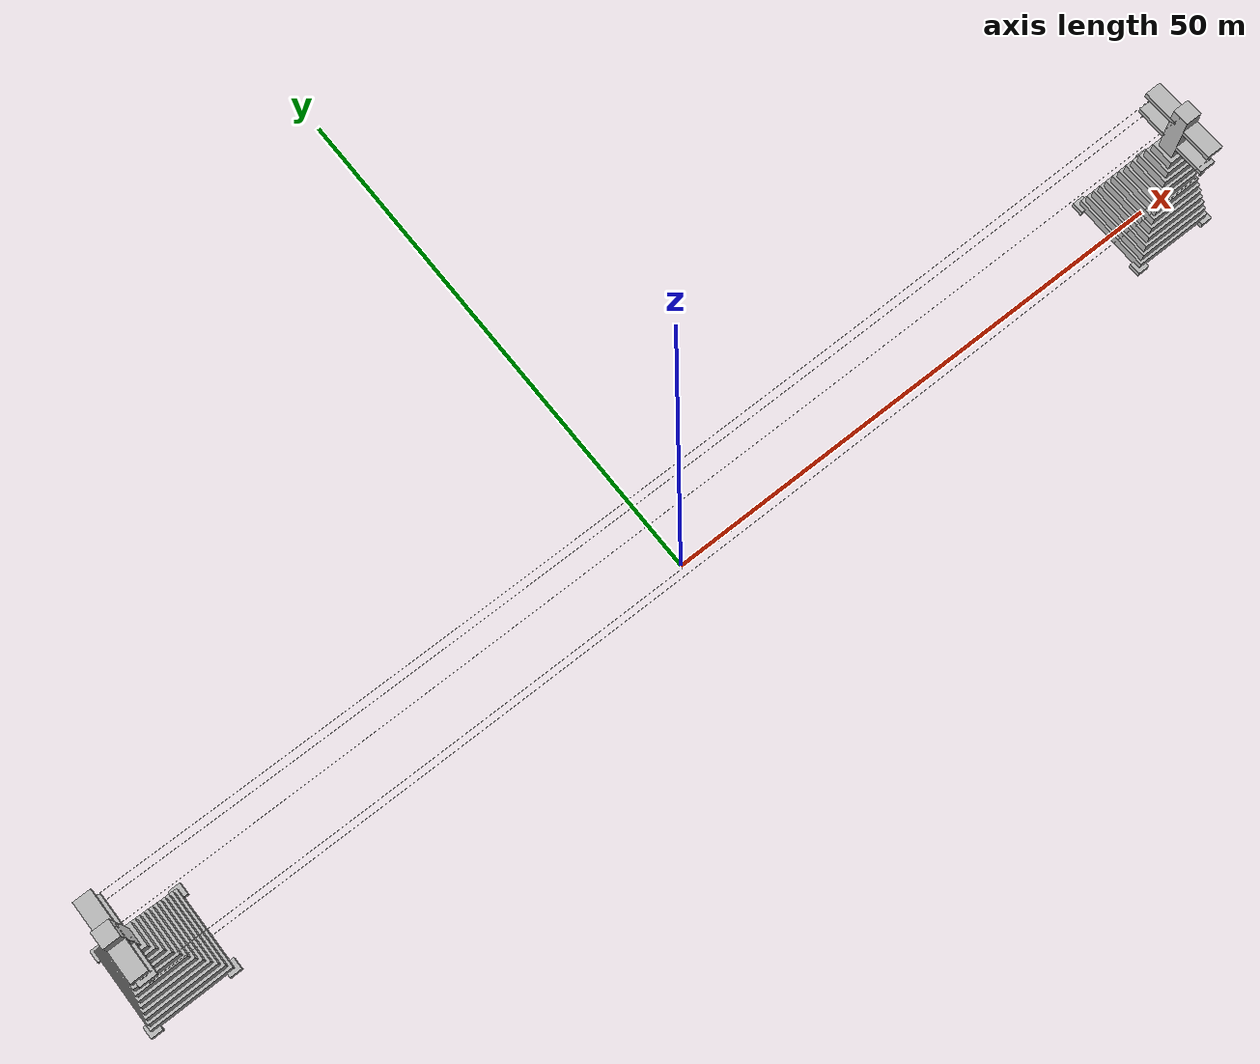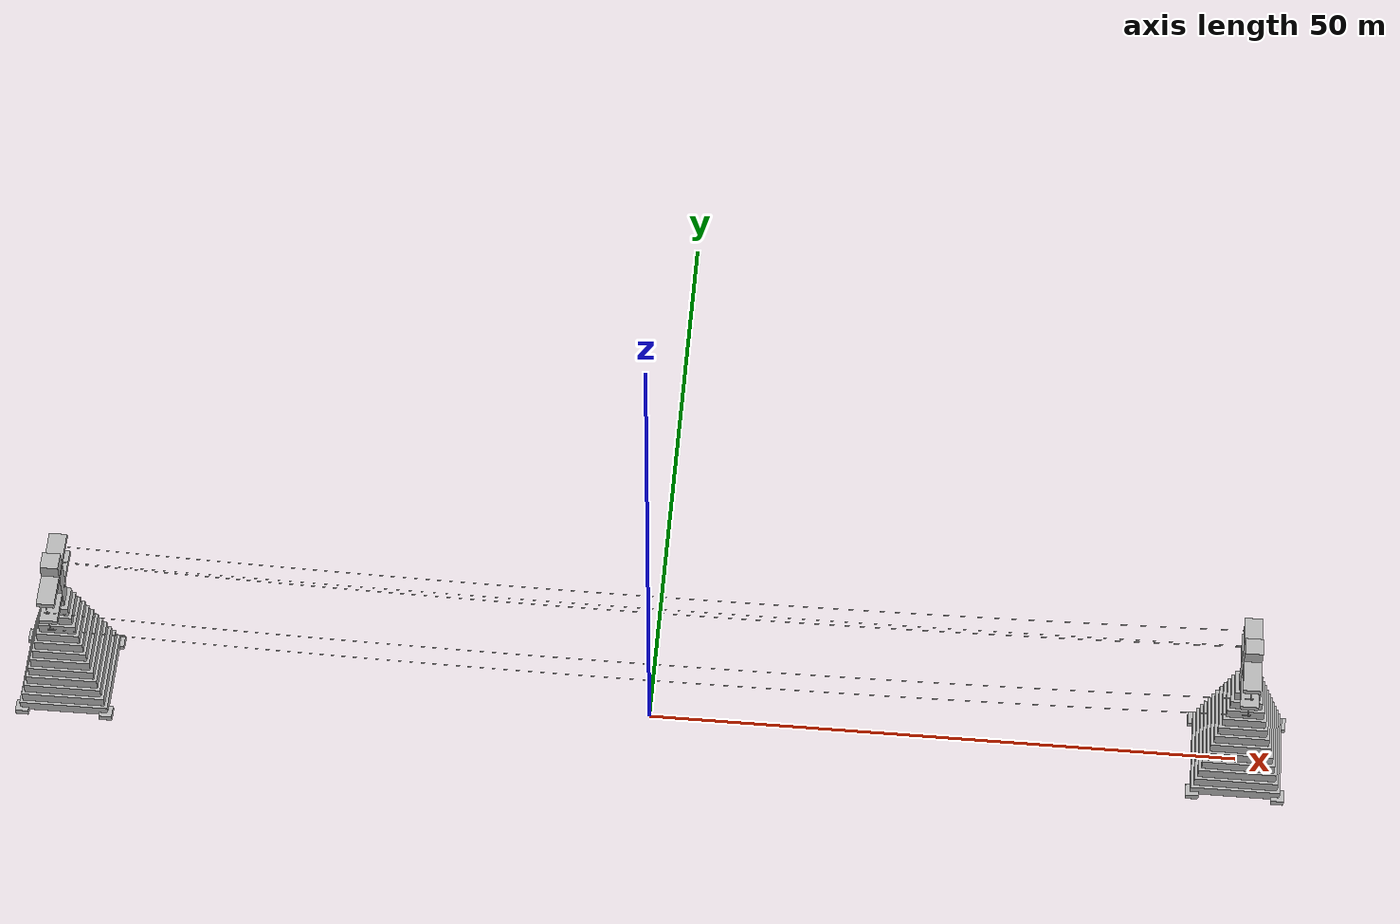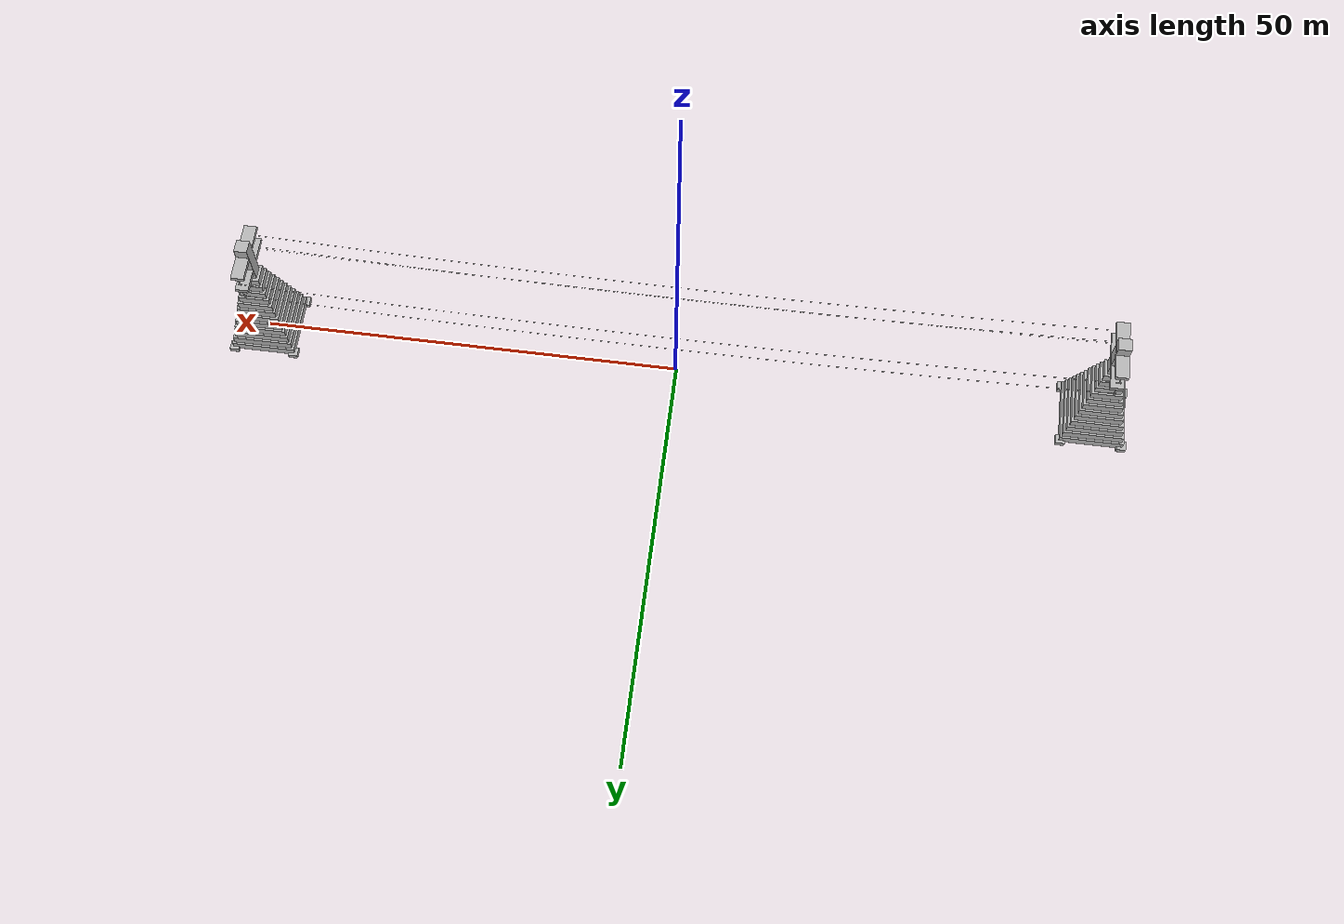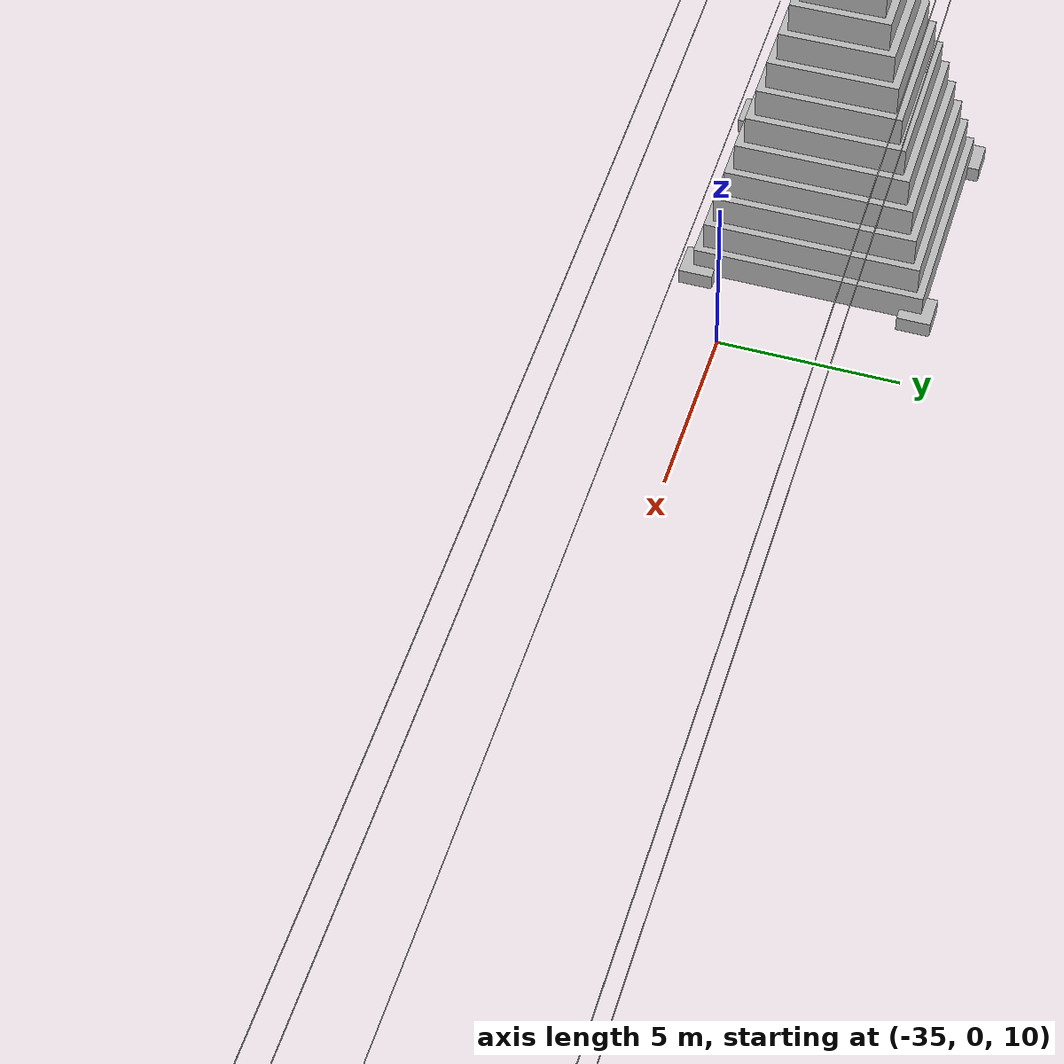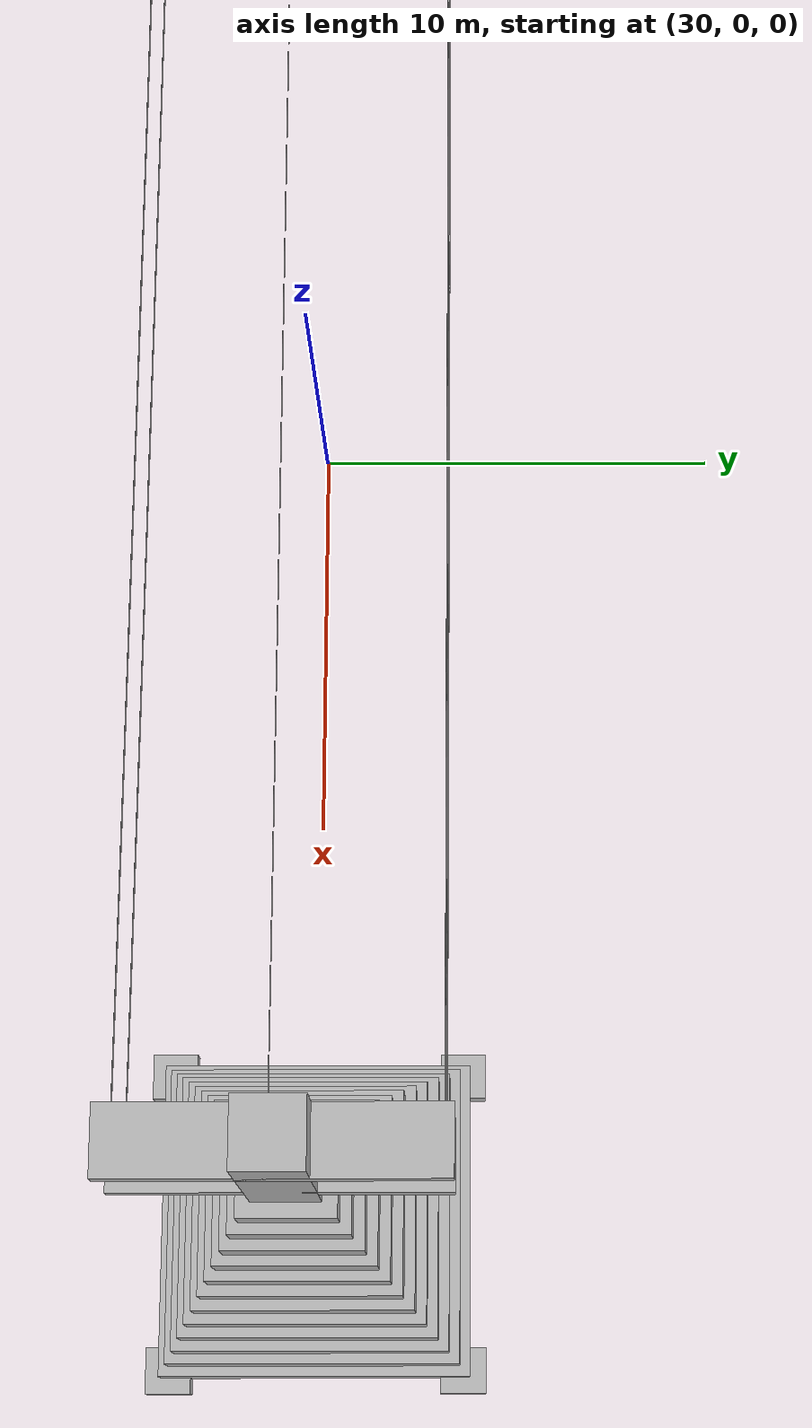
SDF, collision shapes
<?xml version='1.0' encoding='utf-8'?>
<sdf version="1.10">
  <model name="powerline_corridor">
    <static>true</static>
    <link name="corridor">
      <visual name="tower_0_steel">
        <pose>-50 0 3.7708724 0 0 0</pose>
        <geometry>
          <mesh>
            <uri>model://powerline_corridor/meshes/steel.stl</uri>
          </mesh>
        </geometry>
        <material>
          <ambient>.48 .53 .58 1</ambient>
          <diffuse>.48 .53 .58 1</diffuse>
          <specular>.25 .25 .25 1</specular>
        </material>
      </visual>
      <visual name="tower_0_insulators">
        <pose>-50 0 3.7708724 0 0 0</pose>
        <geometry>
          <mesh>
            <uri>model://powerline_corridor/meshes/insulators.stl</uri>
          </mesh>
        </geometry>
        <material>
          <ambient>.16 .42 .36 1</ambient>
          <diffuse>.16 .42 .36 1</diffuse>
          <specular>.25 .25 .25 1</specular>
        </material>
      </visual>
      <visual name="footing_0_0">
        <pose>-53.6 -3.6 0.05 0 0 0</pose>
        <geometry>
          <box>
            <size>1.1 1.1 0.55</size>
          </box>
        </geometry>
        <material>
          <ambient>.56 .56 .53 1</ambient>
          <diffuse>.56 .56 .53 1</diffuse>
          <specular>.25 .25 .25 1</specular>
        </material>
      </visual>
      <visual name="footing_0_1">
        <pose>-53.6 3.6 0.05 0 0 0</pose>
        <geometry>
          <box>
            <size>1.1 1.1 0.55</size>
          </box>
        </geometry>
        <material>
          <ambient>.56 .56 .53 1</ambient>
          <diffuse>.56 .56 .53 1</diffuse>
          <specular>.25 .25 .25 1</specular>
        </material>
      </visual>
      <visual name="footing_0_2">
        <pose>-46.4 -3.6 0.05 0 0 0</pose>
        <geometry>
          <box>
            <size>1.1 1.1 0.55</size>
          </box>
        </geometry>
        <material>
          <ambient>.56 .56 .53 1</ambient>
          <diffuse>.56 .56 .53 1</diffuse>
          <specular>.25 .25 .25 1</specular>
        </material>
      </visual>
      <visual name="footing_0_3">
        <pose>-46.4 3.6 0.05 0 0 0</pose>
        <geometry>
          <box>
            <size>1.1 1.1 0.55</size>
          </box>
        </geometry>
        <material>
          <ambient>.56 .56 .53 1</ambient>
          <diffuse>.56 .56 .53 1</diffuse>
          <specular>.25 .25 .25 1</specular>
        </material>
      </visual>
      <visual name="plate_0">
        <pose>-50 -2.4 5 0 0 0</pose>
        <geometry>
          <box>
            <size>1.0 0.025 0.6</size>
          </box>
        </geometry>
        <material>
          <ambient>.18 .27 .31 1</ambient>
          <diffuse>.18 .27 .31 1</diffuse>
          <specular>.25 .25 .25 1</specular>
        </material>
      </visual>
      <visual name="tower_1_steel">
        <pose>50 0 3.7708724 0 0 0</pose>
        <geometry>
          <mesh>
            <uri>model://powerline_corridor/meshes/steel.stl</uri>
          </mesh>
        </geometry>
        <material>
          <ambient>.48 .53 .58 1</ambient>
          <diffuse>.48 .53 .58 1</diffuse>
          <specular>.25 .25 .25 1</specular>
        </material>
      </visual>
      <visual name="tower_1_insulators">
        <pose>50 0 3.7708724 0 0 0</pose>
        <geometry>
          <mesh>
            <uri>model://powerline_corridor/meshes/insulators.stl</uri>
          </mesh>
        </geometry>
        <material>
          <ambient>.16 .42 .36 1</ambient>
          <diffuse>.16 .42 .36 1</diffuse>
          <specular>.25 .25 .25 1</specular>
        </material>
      </visual>
      <visual name="footing_1_0">
        <pose>46.4 -3.6 0.05 0 0 0</pose>
        <geometry>
          <box>
            <size>1.1 1.1 0.55</size>
          </box>
        </geometry>
        <material>
          <ambient>.56 .56 .53 1</ambient>
          <diffuse>.56 .56 .53 1</diffuse>
          <specular>.25 .25 .25 1</specular>
        </material>
      </visual>
      <visual name="footing_1_1">
        <pose>46.4 3.6 0.05 0 0 0</pose>
        <geometry>
          <box>
            <size>1.1 1.1 0.55</size>
          </box>
        </geometry>
        <material>
          <ambient>.56 .56 .53 1</ambient>
          <diffuse>.56 .56 .53 1</diffuse>
          <specular>.25 .25 .25 1</specular>
        </material>
      </visual>
      <visual name="footing_1_2">
        <pose>53.6 -3.6 0.05 0 0 0</pose>
        <geometry>
          <box>
            <size>1.1 1.1 0.55</size>
          </box>
        </geometry>
        <material>
          <ambient>.56 .56 .53 1</ambient>
          <diffuse>.56 .56 .53 1</diffuse>
          <specular>.25 .25 .25 1</specular>
        </material>
      </visual>
      <visual name="footing_1_3">
        <pose>53.6 3.6 0.05 0 0 0</pose>
        <geometry>
          <box>
            <size>1.1 1.1 0.55</size>
          </box>
        </geometry>
        <material>
          <ambient>.56 .56 .53 1</ambient>
          <diffuse>.56 .56 .53 1</diffuse>
          <specular>.25 .25 .25 1</specular>
        </material>
      </visual>
      <visual name="plate_1">
        <pose>50 -2.4 5 0 0 0</pose>
        <geometry>
          <box>
            <size>1.0 0.025 0.6</size>
          </box>
        </geometry>
        <material>
          <ambient>.18 .27 .31 1</ambient>
          <diffuse>.18 .27 .31 1</diffuse>
          <specular>.25 .25 .25 1</specular>
        </material>
      </visual>
      <visual name="phase_0_0_core_0">
        <pose>-50.0 -3.35 12.837 0 0.0 0.0</pose>
        <geometry>
          <cylinder>
            <radius>0.035</radius>
            <length>1.0999999999999996</length>
          </cylinder>
        </geometry>
        <material>
          <ambient>.36 .39 .42 1</ambient>
          <diffuse>.36 .39 .42 1</diffuse>
          <specular>.25 .25 .25 1</specular>
        </material>
      </visual>
      <visual name="phase_0_0_clamp_0">
        <pose>-50 -3.35 12.287 0 0 0</pose>
        <geometry>
          <box>
            <size>0.46 0.1 0.1</size>
          </box>
        </geometry>
        <material>
          <ambient>.30 .33 .36 1</ambient>
          <diffuse>.30 .33 .36 1</diffuse>
          <specular>.25 .25 .25 1</specular>
        </material>
      </visual>
      <visual name="phase_0_0_damper_stem_0">
        <pose>-49.2 -3.35 12.15230372708189 0 3.141592653589793 0.0</pose>
        <geometry>
          <cylinder>
            <radius>0.012</radius>
            <length>0.1899999999999995</length>
          </cylinder>
        </geometry>
        <material>
          <ambient>.6 .64 .68 1</ambient>
          <diffuse>.6 .64 .68 1</diffuse>
          <specular>.25 .25 .25 1</specular>
        </material>
      </visual>
      <visual name="phase_0_0_damper_0">
        <pose>-49.2 -3.35 12.05730372708189 0 1.5707963267948966 0.0</pose>
        <geometry>
          <cylinder>
            <radius>0.045</radius>
            <length>0.3199999999999932</length>
          </cylinder>
        </geometry>
        <material>
          <ambient>.26 .28 .3 1</ambient>
          <diffuse>.26 .28 .3 1</diffuse>
          <specular>.25 .25 .25 1</specular>
        </material>
      </visual>
      <visual name="phase_0_0_core_1">
        <pose>50.0 -3.35 12.837 0 0.0 0.0</pose>
        <geometry>
          <cylinder>
            <radius>0.035</radius>
            <length>1.0999999999999996</length>
          </cylinder>
        </geometry>
        <material>
          <ambient>.36 .39 .42 1</ambient>
          <diffuse>.36 .39 .42 1</diffuse>
          <specular>.25 .25 .25 1</specular>
        </material>
      </visual>
      <visual name="phase_0_0_clamp_1">
        <pose>50 -3.35 12.287 0 0 0</pose>
        <geometry>
          <box>
            <size>0.46 0.1 0.1</size>
          </box>
        </geometry>
        <material>
          <ambient>.30 .33 .36 1</ambient>
          <diffuse>.30 .33 .36 1</diffuse>
          <specular>.25 .25 .25 1</specular>
        </material>
      </visual>
      <visual name="phase_0_0_damper_stem_1">
        <pose>49.2 -3.35 12.15230372708189 0 3.141592653589793 0.0</pose>
        <geometry>
          <cylinder>
            <radius>0.012</radius>
            <length>0.1899999999999995</length>
          </cylinder>
        </geometry>
        <material>
          <ambient>.6 .64 .68 1</ambient>
          <diffuse>.6 .64 .68 1</diffuse>
          <specular>.25 .25 .25 1</specular>
        </material>
      </visual>
      <visual name="phase_0_0_damper_1">
        <pose>49.2 -3.35 12.05730372708189 0 1.5707963267948966 0.0</pose>
        <geometry>
          <cylinder>
            <radius>0.045</radius>
            <length>0.3199999999999932</length>
          </cylinder>
        </geometry>
        <material>
          <ambient>.26 .28 .3 1</ambient>
          <diffuse>.26 .28 .3 1</diffuse>
          <specular>.25 .25 .25 1</specular>
        </material>
      </visual>
      <visual name="phase_0_1_core_0">
        <pose>-50.0 3.35 12.837 0 0.0 0.0</pose>
        <geometry>
          <cylinder>
            <radius>0.035</radius>
            <length>1.0999999999999996</length>
          </cylinder>
        </geometry>
        <material>
          <ambient>.36 .39 .42 1</ambient>
          <diffuse>.36 .39 .42 1</diffuse>
          <specular>.25 .25 .25 1</specular>
        </material>
      </visual>
      <visual name="phase_0_1_clamp_0">
        <pose>-50 3.35 12.287 0 0 0</pose>
        <geometry>
          <box>
            <size>0.46 0.1 0.1</size>
          </box>
        </geometry>
        <material>
          <ambient>.30 .33 .36 1</ambient>
          <diffuse>.30 .33 .36 1</diffuse>
          <specular>.25 .25 .25 1</specular>
        </material>
      </visual>
      <visual name="phase_0_1_damper_stem_0">
        <pose>-49.2 3.35 12.15230372708189 0 3.141592653589793 0.0</pose>
        <geometry>
          <cylinder>
            <radius>0.012</radius>
            <length>0.1899999999999995</length>
          </cylinder>
        </geometry>
        <material>
          <ambient>.6 .64 .68 1</ambient>
          <diffuse>.6 .64 .68 1</diffuse>
          <specular>.25 .25 .25 1</specular>
        </material>
      </visual>
      <visual name="phase_0_1_damper_0">
        <pose>-49.2 3.35 12.05730372708189 0 1.5707963267948966 0.0</pose>
        <geometry>
          <cylinder>
            <radius>0.045</radius>
            <length>0.3199999999999932</length>
          </cylinder>
        </geometry>
        <material>
          <ambient>.26 .28 .3 1</ambient>
          <diffuse>.26 .28 .3 1</diffuse>
          <specular>.25 .25 .25 1</specular>
        </material>
      </visual>
      <visual name="phase_0_1_core_1">
        <pose>50.0 3.35 12.837 0 0.0 0.0</pose>
        <geometry>
          <cylinder>
            <radius>0.035</radius>
            <length>1.0999999999999996</length>
          </cylinder>
        </geometry>
        <material>
          <ambient>.36 .39 .42 1</ambient>
          <diffuse>.36 .39 .42 1</diffuse>
          <specular>.25 .25 .25 1</specular>
        </material>
      </visual>
      <visual name="phase_0_1_clamp_1">
        <pose>50 3.35 12.287 0 0 0</pose>
        <geometry>
          <box>
            <size>0.46 0.1 0.1</size>
          </box>
        </geometry>
        <material>
          <ambient>.30 .33 .36 1</ambient>
          <diffuse>.30 .33 .36 1</diffuse>
          <specular>.25 .25 .25 1</specular>
        </material>
      </visual>
      <visual name="phase_0_1_damper_stem_1">
        <pose>49.2 3.35 12.15230372708189 0 3.141592653589793 0.0</pose>
        <geometry>
          <cylinder>
            <radius>0.012</radius>
            <length>0.1899999999999995</length>
          </cylinder>
        </geometry>
        <material>
          <ambient>.6 .64 .68 1</ambient>
          <diffuse>.6 .64 .68 1</diffuse>
          <specular>.25 .25 .25 1</specular>
        </material>
      </visual>
      <visual name="phase_0_1_damper_1">
        <pose>49.2 3.35 12.05730372708189 0 1.5707963267948966 0.0</pose>
        <geometry>
          <cylinder>
            <radius>0.045</radius>
            <length>0.3199999999999932</length>
          </cylinder>
        </geometry>
        <material>
          <ambient>.26 .28 .3 1</ambient>
          <diffuse>.26 .28 .3 1</diffuse>
          <specular>.25 .25 .25 1</specular>
        </material>
      </visual>
      <visual name="phase_1_0_core_0">
        <pose>-50.0 -3.35 15.337 0 0.0 0.0</pose>
        <geometry>
          <cylinder>
            <radius>0.035</radius>
            <length>1.0999999999999996</length>
          </cylinder>
        </geometry>
        <material>
          <ambient>.36 .39 .42 1</ambient>
          <diffuse>.36 .39 .42 1</diffuse>
          <specular>.25 .25 .25 1</specular>
        </material>
      </visual>
      <visual name="phase_1_0_clamp_0">
        <pose>-50 -3.35 14.787 0 0 0</pose>
        <geometry>
          <box>
            <size>0.46 0.1 0.1</size>
          </box>
        </geometry>
        <material>
          <ambient>.30 .33 .36 1</ambient>
          <diffuse>.30 .33 .36 1</diffuse>
          <specular>.25 .25 .25 1</specular>
        </material>
      </visual>
      <visual name="phase_1_0_damper_stem_0">
        <pose>-49.2 -3.35 14.65230372708189 0 3.141592653589793 0.0</pose>
        <geometry>
          <cylinder>
            <radius>0.012</radius>
            <length>0.1899999999999995</length>
          </cylinder>
        </geometry>
        <material>
          <ambient>.6 .64 .68 1</ambient>
          <diffuse>.6 .64 .68 1</diffuse>
          <specular>.25 .25 .25 1</specular>
        </material>
      </visual>
      <visual name="phase_1_0_damper_0">
        <pose>-49.2 -3.35 14.55730372708189 0 1.5707963267948966 0.0</pose>
        <geometry>
          <cylinder>
            <radius>0.045</radius>
            <length>0.3199999999999932</length>
          </cylinder>
        </geometry>
        <material>
          <ambient>.26 .28 .3 1</ambient>
          <diffuse>.26 .28 .3 1</diffuse>
          <specular>.25 .25 .25 1</specular>
        </material>
      </visual>
      <visual name="phase_1_0_core_1">
        <pose>50.0 -3.35 15.337 0 0.0 0.0</pose>
        <geometry>
          <cylinder>
            <radius>0.035</radius>
            <length>1.0999999999999996</length>
          </cylinder>
        </geometry>
        <material>
          <ambient>.36 .39 .42 1</ambient>
          <diffuse>.36 .39 .42 1</diffuse>
          <specular>.25 .25 .25 1</specular>
        </material>
      </visual>
      <visual name="phase_1_0_clamp_1">
        <pose>50 -3.35 14.787 0 0 0</pose>
        <geometry>
          <box>
            <size>0.46 0.1 0.1</size>
          </box>
        </geometry>
        <material>
          <ambient>.30 .33 .36 1</ambient>
          <diffuse>.30 .33 .36 1</diffuse>
          <specular>.25 .25 .25 1</specular>
        </material>
      </visual>
      <visual name="phase_1_0_damper_stem_1">
        <pose>49.2 -3.35 14.65230372708189 0 3.141592653589793 0.0</pose>
        <geometry>
          <cylinder>
            <radius>0.012</radius>
            <length>0.1899999999999995</length>
          </cylinder>
        </geometry>
        <material>
          <ambient>.6 .64 .68 1</ambient>
          <diffuse>.6 .64 .68 1</diffuse>
          <specular>.25 .25 .25 1</specular>
        </material>
      </visual>
      <visual name="phase_1_0_damper_1">
        <pose>49.2 -3.35 14.55730372708189 0 1.5707963267948966 0.0</pose>
        <geometry>
          <cylinder>
            <radius>0.045</radius>
            <length>0.3199999999999932</length>
          </cylinder>
        </geometry>
        <material>
          <ambient>.26 .28 .3 1</ambient>
          <diffuse>.26 .28 .3 1</diffuse>
          <specular>.25 .25 .25 1</specular>
        </material>
      </visual>
      <visual name="phase_1_1_core_0">
        <pose>-50.0 3.35 15.337 0 0.0 0.0</pose>
        <geometry>
          <cylinder>
            <radius>0.035</radius>
            <length>1.0999999999999996</length>
          </cylinder>
        </geometry>
        <material>
          <ambient>.36 .39 .42 1</ambient>
          <diffuse>.36 .39 .42 1</diffuse>
          <specular>.25 .25 .25 1</specular>
        </material>
      </visual>
      <visual name="phase_1_1_clamp_0">
        <pose>-50 3.35 14.787 0 0 0</pose>
        <geometry>
          <box>
            <size>0.46 0.1 0.1</size>
          </box>
        </geometry>
        <material>
          <ambient>.30 .33 .36 1</ambient>
          <diffuse>.30 .33 .36 1</diffuse>
          <specular>.25 .25 .25 1</specular>
        </material>
      </visual>
      <visual name="phase_1_1_damper_stem_0">
        <pose>-49.2 3.35 14.65230372708189 0 3.141592653589793 0.0</pose>
        <geometry>
          <cylinder>
            <radius>0.012</radius>
            <length>0.1899999999999995</length>
          </cylinder>
        </geometry>
        <material>
          <ambient>.6 .64 .68 1</ambient>
          <diffuse>.6 .64 .68 1</diffuse>
          <specular>.25 .25 .25 1</specular>
        </material>
      </visual>
      <visual name="phase_1_1_damper_0">
        <pose>-49.2 3.35 14.55730372708189 0 1.5707963267948966 0.0</pose>
        <geometry>
          <cylinder>
            <radius>0.045</radius>
            <length>0.3199999999999932</length>
          </cylinder>
        </geometry>
        <material>
          <ambient>.26 .28 .3 1</ambient>
          <diffuse>.26 .28 .3 1</diffuse>
          <specular>.25 .25 .25 1</specular>
        </material>
      </visual>
      <visual name="phase_1_1_core_1">
        <pose>50.0 3.35 15.337 0 0.0 0.0</pose>
        <geometry>
          <cylinder>
            <radius>0.035</radius>
            <length>1.0999999999999996</length>
          </cylinder>
        </geometry>
        <material>
          <ambient>.36 .39 .42 1</ambient>
          <diffuse>.36 .39 .42 1</diffuse>
          <specular>.25 .25 .25 1</specular>
        </material>
      </visual>
      <visual name="phase_1_1_clamp_1">
        <pose>50 3.35 14.787 0 0 0</pose>
        <geometry>
          <box>
            <size>0.46 0.1 0.1</size>
          </box>
        </geometry>
        <material>
          <ambient>.30 .33 .36 1</ambient>
          <diffuse>.30 .33 .36 1</diffuse>
          <specular>.25 .25 .25 1</specular>
        </material>
      </visual>
      <visual name="phase_1_1_damper_stem_1">
        <pose>49.2 3.35 14.65230372708189 0 3.141592653589793 0.0</pose>
        <geometry>
          <cylinder>
            <radius>0.012</radius>
            <length>0.1899999999999995</length>
          </cylinder>
        </geometry>
        <material>
          <ambient>.6 .64 .68 1</ambient>
          <diffuse>.6 .64 .68 1</diffuse>
          <specular>.25 .25 .25 1</specular>
        </material>
      </visual>
      <visual name="phase_1_1_damper_1">
        <pose>49.2 3.35 14.55730372708189 0 1.5707963267948966 0.0</pose>
        <geometry>
          <cylinder>
            <radius>0.045</radius>
            <length>0.3199999999999932</length>
          </cylinder>
        </geometry>
        <material>
          <ambient>.26 .28 .3 1</ambient>
          <diffuse>.26 .28 .3 1</diffuse>
          <specular>.25 .25 .25 1</specular>
        </material>
      </visual>
      <visual name="phase_0_0">
        <pose>0 0 0 0 0 0</pose>
        <geometry>
          <mesh>
            <uri>model://powerline_corridor/meshes/phase_0_0.stl</uri>
          </mesh>
        </geometry>
        <material>
          <ambient>.63 .66 .69 1</ambient>
          <diffuse>.63 .66 .69 1</diffuse>
          <specular>.25 .25 .25 1</specular>
        </material>
      </visual>
      <visual name="phase_0_1">
        <pose>0 0 0 0 0 0</pose>
        <geometry>
          <mesh>
            <uri>model://powerline_corridor/meshes/phase_0_1.stl</uri>
          </mesh>
        </geometry>
        <material>
          <ambient>.63 .66 .69 1</ambient>
          <diffuse>.63 .66 .69 1</diffuse>
          <specular>.25 .25 .25 1</specular>
        </material>
      </visual>
      <visual name="phase_1_0">
        <pose>0 0 0 0 0 0</pose>
        <geometry>
          <mesh>
            <uri>model://powerline_corridor/meshes/phase_1_0.stl</uri>
          </mesh>
        </geometry>
        <material>
          <ambient>.63 .66 .69 1</ambient>
          <diffuse>.63 .66 .69 1</diffuse>
          <specular>.25 .25 .25 1</specular>
        </material>
      </visual>
      <visual name="phase_1_1">
        <pose>0 0 0 0 0 0</pose>
        <geometry>
          <mesh>
            <uri>model://powerline_corridor/meshes/phase_1_1.stl</uri>
          </mesh>
        </geometry>
        <material>
          <ambient>.63 .66 .69 1</ambient>
          <diffuse>.63 .66 .69 1</diffuse>
          <specular>.25 .25 .25 1</specular>
        </material>
      </visual>
      <visual name="earth_wire">
        <pose>0 0 0 0 0 0</pose>
        <geometry>
          <mesh>
            <uri>model://powerline_corridor/meshes/earth_wire.stl</uri>
          </mesh>
        </geometry>
        <material>
          <ambient>.40 .43 .46 1</ambient>
          <diffuse>.40 .43 .46 1</diffuse>
          <specular>.25 .25 .25 1</specular>
        </material>
      </visual>
    </link>
    <link name="span_collision_10">
      <collision name="tower_0_envelope_0">
        <pose>-50 0 0.5 0 0 0</pose>
        <geometry>
          <box>
            <size>7.54 7.54 1</size>
          </box>
        </geometry>
      </collision>
      <collision name="tower_0_envelope_1">
        <pose>-50 0 1.5 0 0 0</pose>
        <geometry>
          <box>
            <size>7.05 7.05 1</size>
          </box>
        </geometry>
      </collision>
      <collision name="tower_0_envelope_2">
        <pose>-50 0 2.5 0 0 0</pose>
        <geometry>
          <box>
            <size>6.5600000000000005 6.5600000000000005 1</size>
          </box>
        </geometry>
      </collision>
      <collision name="tower_0_envelope_3">
        <pose>-50 0 3.5 0 0 0</pose>
        <geometry>
          <box>
            <size>6.07 6.07 1</size>
          </box>
        </geometry>
      </collision>
      <collision name="tower_0_envelope_4">
        <pose>-50 0 4.5 0 0 0</pose>
        <geometry>
          <box>
            <size>5.58 5.58 1</size>
          </box>
        </geometry>
      </collision>
      <collision name="tower_0_envelope_5">
        <pose>-50 0 5.5 0 0 0</pose>
        <geometry>
          <box>
            <size>5.09 5.09 1</size>
          </box>
        </geometry>
      </collision>
      <collision name="tower_0_envelope_6">
        <pose>-50 0 6.5 0 0 0</pose>
        <geometry>
          <box>
            <size>4.6 4.6 1</size>
          </box>
        </geometry>
      </collision>
      <collision name="tower_0_envelope_7">
        <pose>-50 0 7.5 0 0 0</pose>
        <geometry>
          <box>
            <size>4.11 4.11 1</size>
          </box>
        </geometry>
      </collision>
      <collision name="tower_0_envelope_8">
        <pose>-50 0 8.5 0 0 0</pose>
        <geometry>
          <box>
            <size>3.62 3.62 1</size>
          </box>
        </geometry>
      </collision>
      <collision name="tower_0_envelope_9">
        <pose>-50 0 9.5 0 0 0</pose>
        <geometry>
          <box>
            <size>3.13 3.13 1</size>
          </box>
        </geometry>
      </collision>
      <collision name="tower_0_envelope_10">
        <pose>-50 0 10.5 0 0 0</pose>
        <geometry>
          <box>
            <size>2.6399999999999997 2.6399999999999997 1</size>
          </box>
        </geometry>
      </collision>
      <collision name="tower_0_envelope_11">
        <pose>-50 0 11.5 0 0 0</pose>
        <geometry>
          <box>
            <size>2.1500000000000004 2.1500000000000004 1</size>
          </box>
        </geometry>
      </collision>
      <collision name="tower_0_arm_0">
        <pose>-50 0 13.65 0 0 0</pose>
        <geometry>
          <box>
            <size>1.5 7.1 .45</size>
          </box>
        </geometry>
      </collision>
      <collision name="tower_0_arm_1">
        <pose>-50 0 16.15 0 0 0</pose>
        <geometry>
          <box>
            <size>1.5 7.1 .45</size>
          </box>
        </geometry>
      </collision>
      <collision name="tower_0_upper_core">
        <pose>-50 0 14.8 0 0 0</pose>
        <geometry>
          <box>
            <size>1.5 1.5 5.6</size>
          </box>
        </geometry>
      </collision>
      <collision name="footing_0_2_collision">
        <pose>-46.4 -3.6 0.05 0 0 0</pose>
        <geometry>
          <box>
            <size>1.1 1.1 0.55</size>
          </box>
        </geometry>
      </collision>
      <collision name="footing_0_3_collision">
        <pose>-46.4 3.6 0.05 0 0 0</pose>
        <geometry>
          <box>
            <size>1.1 1.1 0.55</size>
          </box>
        </geometry>
      </collision>
      <collision name="phase_0_0_core_0_collision">
        <pose>-50.0 -3.35 12.837 0 0.0 0.0</pose>
        <geometry>
          <cylinder>
            <radius>0.035</radius>
            <length>1.0999999999999996</length>
          </cylinder>
        </geometry>
      </collision>
      <collision name="phase_0_0_clamp_0_collision">
        <pose>-50 -3.35 12.287 0 0 0</pose>
        <geometry>
          <box>
            <size>0.46 0.1 0.1</size>
          </box>
        </geometry>
      </collision>
      <collision name="phase_0_0_0_collision">
        <pose>-49.5 -3.35 12.262239890448676 0 1.6202761266646943 0.0</pose>
        <geometry>
          <cylinder>
            <radius>0.012</radius>
            <length>1.0012253752777016</length>
          </cylinder>
        </geometry>
      </collision>
      <collision name="phase_0_0_1_collision">
        <pose>-48.5 -3.35 12.213220271757926 0 1.6192773259647162 0.0</pose>
        <geometry>
          <cylinder>
            <radius>0.012</radius>
            <length>1.001176355661051</length>
          </cylinder>
        </geometry>
      </collision>
      <collision name="phase_0_0_2_collision">
        <pose>-47.5 -3.35 12.165201829631386 0 1.618278476859848 0.0</pose>
        <geometry>
          <cylinder>
            <radius>0.012</radius>
            <length>1.0011283372209305</length>
          </cylinder>
        </geometry>
      </collision>
      <collision name="phase_0_0_3_collision">
        <pose>-46.5 -3.35 12.118184516050576 0 1.6172795803440743 0.0</pose>
        <geometry>
          <cylinder>
            <radius>0.012</radius>
            <length>1.0010813199093092</length>
          </cylinder>
        </geometry>
      </collision>
      <collision name="phase_0_0_4_collision">
        <pose>-45.5 -3.35 12.072168283998106 0 1.616280637412234 0.0</pose>
        <geometry>
          <cylinder>
            <radius>0.012</radius>
            <length>1.0010353036791855</length>
          </cylinder>
        </geometry>
      </collision>
      <collision name="phase_0_1_core_0_collision">
        <pose>-50.0 3.35 12.837 0 0.0 0.0</pose>
        <geometry>
          <cylinder>
            <radius>0.035</radius>
            <length>1.0999999999999996</length>
          </cylinder>
        </geometry>
      </collision>
      <collision name="phase_0_1_clamp_0_collision">
        <pose>-50 3.35 12.287 0 0 0</pose>
        <geometry>
          <box>
            <size>0.46 0.1 0.1</size>
          </box>
        </geometry>
      </collision>
      <collision name="phase_0_1_0_collision">
        <pose>-49.5 3.35 12.262239890448676 0 1.6202761266646943 0.0</pose>
        <geometry>
          <cylinder>
            <radius>0.012</radius>
            <length>1.0012253752777016</length>
          </cylinder>
        </geometry>
      </collision>
      <collision name="phase_0_1_1_collision">
        <pose>-48.5 3.35 12.213220271757926 0 1.6192773259647162 0.0</pose>
        <geometry>
          <cylinder>
            <radius>0.012</radius>
            <length>1.001176355661051</length>
          </cylinder>
        </geometry>
      </collision>
      <collision name="phase_0_1_2_collision">
        <pose>-47.5 3.35 12.165201829631386 0 1.618278476859848 0.0</pose>
        <geometry>
          <cylinder>
            <radius>0.012</radius>
            <length>1.0011283372209305</length>
          </cylinder>
        </geometry>
      </collision>
      <collision name="phase_0_1_3_collision">
        <pose>-46.5 3.35 12.118184516050576 0 1.6172795803440743 0.0</pose>
        <geometry>
          <cylinder>
            <radius>0.012</radius>
            <length>1.0010813199093092</length>
          </cylinder>
        </geometry>
      </collision>
      <collision name="phase_0_1_4_collision">
        <pose>-45.5 3.35 12.072168283998106 0 1.616280637412234 0.0</pose>
        <geometry>
          <cylinder>
            <radius>0.012</radius>
            <length>1.0010353036791855</length>
          </cylinder>
        </geometry>
      </collision>
      <collision name="phase_1_0_core_0_collision">
        <pose>-50.0 -3.35 15.337 0 0.0 0.0</pose>
        <geometry>
          <cylinder>
            <radius>0.035</radius>
            <length>1.0999999999999996</length>
          </cylinder>
        </geometry>
      </collision>
      <collision name="phase_1_0_clamp_0_collision">
        <pose>-50 -3.35 14.787 0 0 0</pose>
        <geometry>
          <box>
            <size>0.46 0.1 0.1</size>
          </box>
        </geometry>
      </collision>
      <collision name="phase_1_0_0_collision">
        <pose>-49.5 -3.35 14.762239890448676 0 1.6202761266646943 0.0</pose>
        <geometry>
          <cylinder>
            <radius>0.012</radius>
            <length>1.0012253752777016</length>
          </cylinder>
        </geometry>
      </collision>
      <collision name="phase_1_0_1_collision">
        <pose>-48.5 -3.35 14.713220271757926 0 1.6192773259647162 0.0</pose>
        <geometry>
          <cylinder>
            <radius>0.012</radius>
            <length>1.001176355661051</length>
          </cylinder>
        </geometry>
      </collision>
      <collision name="phase_1_0_2_collision">
        <pose>-47.5 -3.35 14.665201829631386 0 1.618278476859848 0.0</pose>
        <geometry>
          <cylinder>
            <radius>0.012</radius>
            <length>1.0011283372209305</length>
          </cylinder>
        </geometry>
      </collision>
      <collision name="phase_1_0_3_collision">
        <pose>-46.5 -3.35 14.618184516050576 0 1.6172795803440743 0.0</pose>
        <geometry>
          <cylinder>
            <radius>0.012</radius>
            <length>1.0010813199093092</length>
          </cylinder>
        </geometry>
      </collision>
      <collision name="phase_1_0_4_collision">
        <pose>-45.5 -3.35 14.572168283998106 0 1.616280637412234 0.0</pose>
        <geometry>
          <cylinder>
            <radius>0.012</radius>
            <length>1.0010353036791855</length>
          </cylinder>
        </geometry>
      </collision>
      <collision name="phase_1_1_core_0_collision">
        <pose>-50.0 3.35 15.337 0 0.0 0.0</pose>
        <geometry>
          <cylinder>
            <radius>0.035</radius>
            <length>1.0999999999999996</length>
          </cylinder>
        </geometry>
      </collision>
      <collision name="phase_1_1_clamp_0_collision">
        <pose>-50 3.35 14.787 0 0 0</pose>
        <geometry>
          <box>
            <size>0.46 0.1 0.1</size>
          </box>
        </geometry>
      </collision>
      <collision name="phase_1_1_0_collision">
        <pose>-49.5 3.35 14.762239890448676 0 1.6202761266646943 0.0</pose>
        <geometry>
          <cylinder>
            <radius>0.012</radius>
            <length>1.0012253752777016</length>
          </cylinder>
        </geometry>
      </collision>
      <collision name="phase_1_1_1_collision">
        <pose>-48.5 3.35 14.713220271757926 0 1.6192773259647162 0.0</pose>
        <geometry>
          <cylinder>
            <radius>0.012</radius>
            <length>1.001176355661051</length>
          </cylinder>
        </geometry>
      </collision>
      <collision name="phase_1_1_2_collision">
        <pose>-47.5 3.35 14.665201829631386 0 1.618278476859848 0.0</pose>
        <geometry>
          <cylinder>
            <radius>0.012</radius>
            <length>1.0011283372209305</length>
          </cylinder>
        </geometry>
      </collision>
      <collision name="phase_1_1_3_collision">
        <pose>-46.5 3.35 14.618184516050576 0 1.6172795803440743 0.0</pose>
        <geometry>
          <cylinder>
            <radius>0.012</radius>
            <length>1.0010813199093092</length>
          </cylinder>
        </geometry>
      </collision>
      <collision name="phase_1_1_4_collision">
        <pose>-45.5 3.35 14.572168283998106 0 1.616280637412234 0.0</pose>
        <geometry>
          <cylinder>
            <radius>0.012</radius>
            <length>1.0010353036791855</length>
          </cylinder>
        </geometry>
      </collision>
      <collision name="earth_wire_0_collision">
        <pose>-49.5 0.0 17.535189362245678 0 1.6004913681310091 0.0</pose>
        <geometry>
          <cylinder>
            <radius>0.008</radius>
            <length>1.000441059790435</length>
          </cylinder>
        </geometry>
      </collision>
      <collision name="earth_wire_1_collision">
        <pose>-48.5 0.0 17.50578571317683 0 1.599891639329742 0.0</pose>
        <geometry>
          <cylinder>
            <radius>0.008</radius>
            <length>1.0004234179540916</length>
          </cylinder>
        </geometry>
      </collision>
      <collision name="earth_wire_2_collision">
        <pose>-47.5 0.0 17.476982306198963 0 1.5992919000606622 0.0</pose>
        <geometry>
          <cylinder>
            <radius>0.008</radius>
            <length>1.0004061362557999</length>
          </cylinder>
        </geometry>
      </collision>
      <collision name="earth_wire_3_collision">
        <pose>-46.5 0.0 17.4487791309433 0 1.5986921505388798 0.0</pose>
        <geometry>
          <cylinder>
            <radius>0.008</radius>
            <length>1.0003892146893258</length>
          </cylinder>
        </geometry>
      </collision>
      <collision name="earth_wire_4_collision">
        <pose>-45.5 0.0 17.42117617725703 0 1.5980923909806386 0.0</pose>
        <geometry>
          <cylinder>
            <radius>0.008</radius>
            <length>1.0003726532485975</length>
          </cylinder>
        </geometry>
      </collision>
    </link>
    <link name="span_collision_9">
      <collision name="footing_0_0_collision">
        <pose>-53.6 -3.6 0.05 0 0 0</pose>
        <geometry>
          <box>
            <size>1.1 1.1 0.55</size>
          </box>
        </geometry>
      </collision>
      <collision name="footing_0_1_collision">
        <pose>-53.6 3.6 0.05 0 0 0</pose>
        <geometry>
          <box>
            <size>1.1 1.1 0.55</size>
          </box>
        </geometry>
      </collision>
    </link>
    <link name="span_collision_30">
      <collision name="tower_1_envelope_0">
        <pose>50 0 0.5 0 0 0</pose>
        <geometry>
          <box>
            <size>7.54 7.54 1</size>
          </box>
        </geometry>
      </collision>
      <collision name="tower_1_envelope_1">
        <pose>50 0 1.5 0 0 0</pose>
        <geometry>
          <box>
            <size>7.05 7.05 1</size>
          </box>
        </geometry>
      </collision>
      <collision name="tower_1_envelope_2">
        <pose>50 0 2.5 0 0 0</pose>
        <geometry>
          <box>
            <size>6.5600000000000005 6.5600000000000005 1</size>
          </box>
        </geometry>
      </collision>
      <collision name="tower_1_envelope_3">
        <pose>50 0 3.5 0 0 0</pose>
        <geometry>
          <box>
            <size>6.07 6.07 1</size>
          </box>
        </geometry>
      </collision>
      <collision name="tower_1_envelope_4">
        <pose>50 0 4.5 0 0 0</pose>
        <geometry>
          <box>
            <size>5.58 5.58 1</size>
          </box>
        </geometry>
      </collision>
      <collision name="tower_1_envelope_5">
        <pose>50 0 5.5 0 0 0</pose>
        <geometry>
          <box>
            <size>5.09 5.09 1</size>
          </box>
        </geometry>
      </collision>
      <collision name="tower_1_envelope_6">
        <pose>50 0 6.5 0 0 0</pose>
        <geometry>
          <box>
            <size>4.6 4.6 1</size>
          </box>
        </geometry>
      </collision>
      <collision name="tower_1_envelope_7">
        <pose>50 0 7.5 0 0 0</pose>
        <geometry>
          <box>
            <size>4.11 4.11 1</size>
          </box>
        </geometry>
      </collision>
      <collision name="tower_1_envelope_8">
        <pose>50 0 8.5 0 0 0</pose>
        <geometry>
          <box>
            <size>3.62 3.62 1</size>
          </box>
        </geometry>
      </collision>
      <collision name="tower_1_envelope_9">
        <pose>50 0 9.5 0 0 0</pose>
        <geometry>
          <box>
            <size>3.13 3.13 1</size>
          </box>
        </geometry>
      </collision>
      <collision name="tower_1_envelope_10">
        <pose>50 0 10.5 0 0 0</pose>
        <geometry>
          <box>
            <size>2.6399999999999997 2.6399999999999997 1</size>
          </box>
        </geometry>
      </collision>
      <collision name="tower_1_envelope_11">
        <pose>50 0 11.5 0 0 0</pose>
        <geometry>
          <box>
            <size>2.1500000000000004 2.1500000000000004 1</size>
          </box>
        </geometry>
      </collision>
      <collision name="tower_1_arm_0">
        <pose>50 0 13.65 0 0 0</pose>
        <geometry>
          <box>
            <size>1.5 7.1 .45</size>
          </box>
        </geometry>
      </collision>
      <collision name="tower_1_arm_1">
        <pose>50 0 16.15 0 0 0</pose>
        <geometry>
          <box>
            <size>1.5 7.1 .45</size>
          </box>
        </geometry>
      </collision>
      <collision name="tower_1_upper_core">
        <pose>50 0 14.8 0 0 0</pose>
        <geometry>
          <box>
            <size>1.5 1.5 5.6</size>
          </box>
        </geometry>
      </collision>
      <collision name="footing_1_2_collision">
        <pose>53.6 -3.6 0.05 0 0 0</pose>
        <geometry>
          <box>
            <size>1.1 1.1 0.55</size>
          </box>
        </geometry>
      </collision>
      <collision name="footing_1_3_collision">
        <pose>53.6 3.6 0.05 0 0 0</pose>
        <geometry>
          <box>
            <size>1.1 1.1 0.55</size>
          </box>
        </geometry>
      </collision>
      <collision name="phase_0_0_core_1_collision">
        <pose>50.0 -3.35 12.837 0 0.0 0.0</pose>
        <geometry>
          <cylinder>
            <radius>0.035</radius>
            <length>1.0999999999999996</length>
          </cylinder>
        </geometry>
      </collision>
      <collision name="phase_0_0_clamp_1_collision">
        <pose>50 -3.35 12.287 0 0 0</pose>
        <geometry>
          <box>
            <size>0.46 0.1 0.1</size>
          </box>
        </geometry>
      </collision>
      <collision name="phase_0_1_core_1_collision">
        <pose>50.0 3.35 12.837 0 0.0 0.0</pose>
        <geometry>
          <cylinder>
            <radius>0.035</radius>
            <length>1.0999999999999996</length>
          </cylinder>
        </geometry>
      </collision>
      <collision name="phase_0_1_clamp_1_collision">
        <pose>50 3.35 12.287 0 0 0</pose>
        <geometry>
          <box>
            <size>0.46 0.1 0.1</size>
          </box>
        </geometry>
      </collision>
      <collision name="phase_1_0_core_1_collision">
        <pose>50.0 -3.35 15.337 0 0.0 0.0</pose>
        <geometry>
          <cylinder>
            <radius>0.035</radius>
            <length>1.0999999999999996</length>
          </cylinder>
        </geometry>
      </collision>
      <collision name="phase_1_0_clamp_1_collision">
        <pose>50 -3.35 14.787 0 0 0</pose>
        <geometry>
          <box>
            <size>0.46 0.1 0.1</size>
          </box>
        </geometry>
      </collision>
      <collision name="phase_1_1_core_1_collision">
        <pose>50.0 3.35 15.337 0 0.0 0.0</pose>
        <geometry>
          <cylinder>
            <radius>0.035</radius>
            <length>1.0999999999999996</length>
          </cylinder>
        </geometry>
      </collision>
      <collision name="phase_1_1_clamp_1_collision">
        <pose>50 3.35 14.787 0 0 0</pose>
        <geometry>
          <box>
            <size>0.46 0.1 0.1</size>
          </box>
        </geometry>
      </collision>
    </link>
    <link name="span_collision_29">
      <collision name="footing_1_0_collision">
        <pose>46.4 -3.6 0.05 0 0 0</pose>
        <geometry>
          <box>
            <size>1.1 1.1 0.55</size>
          </box>
        </geometry>
      </collision>
      <collision name="footing_1_1_collision">
        <pose>46.4 3.6 0.05 0 0 0</pose>
        <geometry>
          <box>
            <size>1.1 1.1 0.55</size>
          </box>
        </geometry>
      </collision>
      <collision name="phase_0_0_95_collision">
        <pose>45.5 -3.35 12.072168283998106 0 1.525312016177559 0.0</pose>
        <geometry>
          <cylinder>
            <radius>0.012</radius>
            <length>1.0010353036791855</length>
          </cylinder>
        </geometry>
      </collision>
      <collision name="phase_0_0_96_collision">
        <pose>46.5 -3.35 12.118184516050576 0 1.5243130732457189 0.0</pose>
        <geometry>
          <cylinder>
            <radius>0.012</radius>
            <length>1.0010813199093092</length>
          </cylinder>
        </geometry>
      </collision>
      <collision name="phase_0_0_97_collision">
        <pose>47.5 -3.35 12.165201829631386 0 1.5233141767299454 0.0</pose>
        <geometry>
          <cylinder>
            <radius>0.012</radius>
            <length>1.0011283372209305</length>
          </cylinder>
        </geometry>
      </collision>
      <collision name="phase_0_0_98_collision">
        <pose>48.5 -3.35 12.213220271757926 0 1.5223153276250772 0.0</pose>
        <geometry>
          <cylinder>
            <radius>0.012</radius>
            <length>1.001176355661051</length>
          </cylinder>
        </geometry>
      </collision>
      <collision name="phase_0_0_99_collision">
        <pose>49.5 -3.35 12.262239890448676 0 1.521316526925099 0.0</pose>
        <geometry>
          <cylinder>
            <radius>0.012</radius>
            <length>1.0012253752777016</length>
          </cylinder>
        </geometry>
      </collision>
      <collision name="phase_0_1_95_collision">
        <pose>45.5 3.35 12.072168283998106 0 1.525312016177559 0.0</pose>
        <geometry>
          <cylinder>
            <radius>0.012</radius>
            <length>1.0010353036791855</length>
          </cylinder>
        </geometry>
      </collision>
      <collision name="phase_0_1_96_collision">
        <pose>46.5 3.35 12.118184516050576 0 1.5243130732457189 0.0</pose>
        <geometry>
          <cylinder>
            <radius>0.012</radius>
            <length>1.0010813199093092</length>
          </cylinder>
        </geometry>
      </collision>
      <collision name="phase_0_1_97_collision">
        <pose>47.5 3.35 12.165201829631386 0 1.5233141767299454 0.0</pose>
        <geometry>
          <cylinder>
            <radius>0.012</radius>
            <length>1.0011283372209305</length>
          </cylinder>
        </geometry>
      </collision>
      <collision name="phase_0_1_98_collision">
        <pose>48.5 3.35 12.213220271757926 0 1.5223153276250772 0.0</pose>
        <geometry>
          <cylinder>
            <radius>0.012</radius>
            <length>1.001176355661051</length>
          </cylinder>
        </geometry>
      </collision>
      <collision name="phase_0_1_99_collision">
        <pose>49.5 3.35 12.262239890448676 0 1.521316526925099 0.0</pose>
        <geometry>
          <cylinder>
            <radius>0.012</radius>
            <length>1.0012253752777016</length>
          </cylinder>
        </geometry>
      </collision>
      <collision name="phase_1_0_95_collision">
        <pose>45.5 -3.35 14.572168283998106 0 1.525312016177559 0.0</pose>
        <geometry>
          <cylinder>
            <radius>0.012</radius>
            <length>1.0010353036791855</length>
          </cylinder>
        </geometry>
      </collision>
      <collision name="phase_1_0_96_collision">
        <pose>46.5 -3.35 14.618184516050576 0 1.5243130732457189 0.0</pose>
        <geometry>
          <cylinder>
            <radius>0.012</radius>
            <length>1.0010813199093092</length>
          </cylinder>
        </geometry>
      </collision>
      <collision name="phase_1_0_97_collision">
        <pose>47.5 -3.35 14.665201829631386 0 1.5233141767299454 0.0</pose>
        <geometry>
          <cylinder>
            <radius>0.012</radius>
            <length>1.0011283372209305</length>
          </cylinder>
        </geometry>
      </collision>
      <collision name="phase_1_0_98_collision">
        <pose>48.5 -3.35 14.713220271757926 0 1.5223153276250772 0.0</pose>
        <geometry>
          <cylinder>
            <radius>0.012</radius>
            <length>1.001176355661051</length>
          </cylinder>
        </geometry>
      </collision>
      <collision name="phase_1_0_99_collision">
        <pose>49.5 -3.35 14.762239890448676 0 1.521316526925099 0.0</pose>
        <geometry>
          <cylinder>
            <radius>0.012</radius>
            <length>1.0012253752777016</length>
          </cylinder>
        </geometry>
      </collision>
      <collision name="phase_1_1_95_collision">
        <pose>45.5 3.35 14.572168283998106 0 1.525312016177559 0.0</pose>
        <geometry>
          <cylinder>
            <radius>0.012</radius>
            <length>1.0010353036791855</length>
          </cylinder>
        </geometry>
      </collision>
      <collision name="phase_1_1_96_collision">
        <pose>46.5 3.35 14.618184516050576 0 1.5243130732457189 0.0</pose>
        <geometry>
          <cylinder>
            <radius>0.012</radius>
            <length>1.0010813199093092</length>
          </cylinder>
        </geometry>
      </collision>
      <collision name="phase_1_1_97_collision">
        <pose>47.5 3.35 14.665201829631386 0 1.5233141767299454 0.0</pose>
        <geometry>
          <cylinder>
            <radius>0.012</radius>
            <length>1.0011283372209305</length>
          </cylinder>
        </geometry>
      </collision>
      <collision name="phase_1_1_98_collision">
        <pose>48.5 3.35 14.713220271757926 0 1.5223153276250772 0.0</pose>
        <geometry>
          <cylinder>
            <radius>0.012</radius>
            <length>1.001176355661051</length>
          </cylinder>
        </geometry>
      </collision>
      <collision name="phase_1_1_99_collision">
        <pose>49.5 3.35 14.762239890448676 0 1.521316526925099 0.0</pose>
        <geometry>
          <cylinder>
            <radius>0.012</radius>
            <length>1.0012253752777016</length>
          </cylinder>
        </geometry>
      </collision>
      <collision name="earth_wire_95_collision">
        <pose>45.5 0.0 17.42117617725703 0 1.5435002626091545 0.0</pose>
        <geometry>
          <cylinder>
            <radius>0.008</radius>
            <length>1.0003726532485975</length>
          </cylinder>
        </geometry>
      </collision>
      <collision name="earth_wire_96_collision">
        <pose>46.5 0.0 17.4487791309433 0 1.5429005030509133 0.0</pose>
        <geometry>
          <cylinder>
            <radius>0.008</radius>
            <length>1.0003892146893258</length>
          </cylinder>
        </geometry>
      </collision>
      <collision name="earth_wire_97_collision">
        <pose>47.5 0.0 17.476982306198963 0 1.542300753529131 0.0</pose>
        <geometry>
          <cylinder>
            <radius>0.008</radius>
            <length>1.0004061362557999</length>
          </cylinder>
        </geometry>
      </collision>
      <collision name="earth_wire_98_collision">
        <pose>48.5 0.0 17.50578571317683 0 1.5417010142600511 0.0</pose>
        <geometry>
          <cylinder>
            <radius>0.008</radius>
            <length>1.0004234179540916</length>
          </cylinder>
        </geometry>
      </collision>
      <collision name="earth_wire_99_collision">
        <pose>49.5 0.0 17.535189362245678 0 1.5411012854587842 0.0</pose>
        <geometry>
          <cylinder>
            <radius>0.008</radius>
            <length>1.000441059790435</length>
          </cylinder>
        </geometry>
      </collision>
    </link>
    <link name="span_collision_11">
      <collision name="phase_0_0_5_collision">
        <pose>-44.5 -3.35 12.027153087457783 0 1.6152816490584645 0.0</pose>
        <geometry>
          <cylinder>
            <radius>0.012</radius>
            <length>1.0009902884845165</length>
          </cylinder>
        </geometry>
      </collision>
      <collision name="phase_0_0_6_collision">
        <pose>-43.5 -3.35 11.983138881414398 0 1.6142826162784136 0.0</pose>
        <geometry>
          <cylinder>
            <radius>0.012</radius>
            <length>1.000946274280319</length>
          </cylinder>
        </geometry>
      </collision>
      <collision name="phase_0_0_7_collision">
        <pose>-42.5 -3.35 11.940125621853712 0 1.6132835400665768 0.0</pose>
        <geometry>
          <cylinder>
            <radius>0.012</radius>
            <length>1.0009032610225486</length>
          </cylinder>
        </geometry>
      </collision>
      <collision name="phase_0_0_8_collision">
        <pose>-41.5 -3.35 11.898113265762465 0 1.6122844214189525 0.0</pose>
        <geometry>
          <cylinder>
            <radius>0.012</radius>
            <length>1.0008612486682185</length>
          </cylinder>
        </geometry>
      </collision>
      <collision name="phase_0_0_9_collision">
        <pose>-40.5 -3.35 11.857101771128374 0 1.611285261330379 0.0</pose>
        <geometry>
          <cylinder>
            <radius>0.012</radius>
            <length>1.0008202371752848</length>
          </cylinder>
        </geometry>
      </collision>
      <collision name="phase_0_1_5_collision">
        <pose>-44.5 3.35 12.027153087457783 0 1.6152816490584645 0.0</pose>
        <geometry>
          <cylinder>
            <radius>0.012</radius>
            <length>1.0009902884845165</length>
          </cylinder>
        </geometry>
      </collision>
      <collision name="phase_0_1_6_collision">
        <pose>-43.5 3.35 11.983138881414398 0 1.6142826162784136 0.0</pose>
        <geometry>
          <cylinder>
            <radius>0.012</radius>
            <length>1.000946274280319</length>
          </cylinder>
        </geometry>
      </collision>
      <collision name="phase_0_1_7_collision">
        <pose>-42.5 3.35 11.940125621853712 0 1.6132835400665768 0.0</pose>
        <geometry>
          <cylinder>
            <radius>0.012</radius>
            <length>1.0009032610225486</length>
          </cylinder>
        </geometry>
      </collision>
      <collision name="phase_0_1_8_collision">
        <pose>-41.5 3.35 11.898113265762465 0 1.6122844214189525 0.0</pose>
        <geometry>
          <cylinder>
            <radius>0.012</radius>
            <length>1.0008612486682185</length>
          </cylinder>
        </geometry>
      </collision>
      <collision name="phase_0_1_9_collision">
        <pose>-40.5 3.35 11.857101771128374 0 1.611285261330379 0.0</pose>
        <geometry>
          <cylinder>
            <radius>0.012</radius>
            <length>1.0008202371752848</length>
          </cylinder>
        </geometry>
      </collision>
      <collision name="phase_1_0_5_collision">
        <pose>-44.5 -3.35 14.527153087457783 0 1.6152816490584645 0.0</pose>
        <geometry>
          <cylinder>
            <radius>0.012</radius>
            <length>1.0009902884845165</length>
          </cylinder>
        </geometry>
      </collision>
      <collision name="phase_1_0_6_collision">
        <pose>-43.5 -3.35 14.483138881414398 0 1.6142826162784136 0.0</pose>
        <geometry>
          <cylinder>
            <radius>0.012</radius>
            <length>1.000946274280319</length>
          </cylinder>
        </geometry>
      </collision>
      <collision name="phase_1_0_7_collision">
        <pose>-42.5 -3.35 14.440125621853712 0 1.6132835400665768 0.0</pose>
        <geometry>
          <cylinder>
            <radius>0.012</radius>
            <length>1.0009032610225486</length>
          </cylinder>
        </geometry>
      </collision>
      <collision name="phase_1_0_8_collision">
        <pose>-41.5 -3.35 14.398113265762465 0 1.6122844214189525 0.0</pose>
        <geometry>
          <cylinder>
            <radius>0.012</radius>
            <length>1.0008612486682185</length>
          </cylinder>
        </geometry>
      </collision>
      <collision name="phase_1_0_9_collision">
        <pose>-40.5 -3.35 14.357101771128374 0 1.611285261330379 0.0</pose>
        <geometry>
          <cylinder>
            <radius>0.012</radius>
            <length>1.0008202371752848</length>
          </cylinder>
        </geometry>
      </collision>
      <collision name="phase_1_1_5_collision">
        <pose>-44.5 3.35 14.527153087457783 0 1.6152816490584645 0.0</pose>
        <geometry>
          <cylinder>
            <radius>0.012</radius>
            <length>1.0009902884845165</length>
          </cylinder>
        </geometry>
      </collision>
      <collision name="phase_1_1_6_collision">
        <pose>-43.5 3.35 14.483138881414398 0 1.6142826162784136 0.0</pose>
        <geometry>
          <cylinder>
            <radius>0.012</radius>
            <length>1.000946274280319</length>
          </cylinder>
        </geometry>
      </collision>
      <collision name="phase_1_1_7_collision">
        <pose>-42.5 3.35 14.440125621853712 0 1.6132835400665768 0.0</pose>
        <geometry>
          <cylinder>
            <radius>0.012</radius>
            <length>1.0009032610225486</length>
          </cylinder>
        </geometry>
      </collision>
      <collision name="phase_1_1_8_collision">
        <pose>-41.5 3.35 14.398113265762465 0 1.6122844214189525 0.0</pose>
        <geometry>
          <cylinder>
            <radius>0.012</radius>
            <length>1.0008612486682185</length>
          </cylinder>
        </geometry>
      </collision>
      <collision name="phase_1_1_9_collision">
        <pose>-40.5 3.35 14.357101771128374 0 1.611285261330379 0.0</pose>
        <geometry>
          <cylinder>
            <radius>0.012</radius>
            <length>1.0008202371752848</length>
          </cylinder>
        </geometry>
      </collision>
      <collision name="earth_wire_5_collision">
        <pose>-44.5 0.0 17.394173435203268 0 1.5974926216010892 0.0</pose>
        <geometry>
          <cylinder>
            <radius>0.008</radius>
            <length>1.0003564519276407</length>
          </cylinder>
        </geometry>
      </collision>
      <collision name="earth_wire_6_collision">
        <pose>-43.5 0.0 17.367770895061632 0 1.596892842615392 0.0</pose>
        <geometry>
          <cylinder>
            <radius>0.008</radius>
            <length>1.0003406107206119</length>
          </cylinder>
        </geometry>
      </collision>
      <collision name="earth_wire_7_collision">
        <pose>-42.5 0.0 17.341968547327685 0 1.59629305423983 0.0</pose>
        <geometry>
          <cylinder>
            <radius>0.008</radius>
            <length>1.0003251296218263</length>
          </cylinder>
        </geometry>
      </collision>
      <collision name="earth_wire_8_collision">
        <pose>-41.5 0.0 17.316766382712927 0 1.5956932566896018 0.0</pose>
        <geometry>
          <cylinder>
            <radius>0.008</radius>
            <length>1.0003100086257002</length>
          </cylinder>
        </geometry>
      </collision>
      <collision name="earth_wire_9_collision">
        <pose>-40.5 0.0 17.292164392144805 0 1.5950934501810023 0.0</pose>
        <geometry>
          <cylinder>
            <radius>0.008</radius>
            <length>1.0002952477268061</length>
          </cylinder>
        </geometry>
      </collision>
    </link>
    <link name="span_collision_12">
      <collision name="phase_0_0_10_collision">
        <pose>-39.5 -3.35 11.817091096939912 0 1.6102860607976321 0.0</pose>
        <geometry>
          <cylinder>
            <radius>0.012</radius>
            <length>1.0007802265027759</length>
          </cylinder>
        </geometry>
      </collision>
      <collision name="phase_0_0_11_collision">
        <pose>-38.5 -3.35 11.778081203186305 0 1.6092868208158773 0.0</pose>
        <geometry>
          <cylinder>
            <radius>0.012</radius>
            <length>1.0007412166106466</length>
          </cylinder>
        </geometry>
      </collision>
      <collision name="phase_0_0_12_collision">
        <pose>-37.5 -3.35 11.740072050857872 0 1.6082875423815441 0.0</pose>
        <geometry>
          <cylinder>
            <radius>0.012</radius>
            <length>1.0007032074598972</length>
          </cylinder>
        </geometry>
      </collision>
      <collision name="phase_0_0_13_collision">
        <pose>-36.5 -3.35 11.703063601945239 0 1.6072882264916604 0.0</pose>
        <geometry>
          <cylinder>
            <radius>0.012</radius>
            <length>1.0006661990125416</length>
          </cylinder>
        </geometry>
      </collision>
      <collision name="phase_0_0_14_collision">
        <pose>-35.5 -3.35 11.667055819440005 0 1.6062888741416288 0.0</pose>
        <geometry>
          <cylinder>
            <radius>0.012</radius>
            <length>1.000630191231528</length>
          </cylinder>
        </geometry>
      </collision>
      <collision name="phase_0_1_10_collision">
        <pose>-39.5 3.35 11.817091096939912 0 1.6102860607976321 0.0</pose>
        <geometry>
          <cylinder>
            <radius>0.012</radius>
            <length>1.0007802265027759</length>
          </cylinder>
        </geometry>
      </collision>
      <collision name="phase_0_1_11_collision">
        <pose>-38.5 3.35 11.778081203186305 0 1.6092868208158773 0.0</pose>
        <geometry>
          <cylinder>
            <radius>0.012</radius>
            <length>1.0007412166106466</length>
          </cylinder>
        </geometry>
      </collision>
      <collision name="phase_0_1_12_collision">
        <pose>-37.5 3.35 11.740072050857872 0 1.6082875423815441 0.0</pose>
        <geometry>
          <cylinder>
            <radius>0.012</radius>
            <length>1.0007032074598972</length>
          </cylinder>
        </geometry>
      </collision>
      <collision name="phase_0_1_13_collision">
        <pose>-36.5 3.35 11.703063601945239 0 1.6072882264916604 0.0</pose>
        <geometry>
          <cylinder>
            <radius>0.012</radius>
            <length>1.0006661990125416</length>
          </cylinder>
        </geometry>
      </collision>
      <collision name="phase_0_1_14_collision">
        <pose>-35.5 3.35 11.667055819440005 0 1.6062888741416288 0.0</pose>
        <geometry>
          <cylinder>
            <radius>0.012</radius>
            <length>1.000630191231528</length>
          </cylinder>
        </geometry>
      </collision>
      <collision name="phase_1_0_10_collision">
        <pose>-39.5 -3.35 14.317091096939912 0 1.6102860607976321 0.0</pose>
        <geometry>
          <cylinder>
            <radius>0.012</radius>
            <length>1.0007802265027759</length>
          </cylinder>
        </geometry>
      </collision>
      <collision name="phase_1_0_11_collision">
        <pose>-38.5 -3.35 14.278081203186305 0 1.6092868208158773 0.0</pose>
        <geometry>
          <cylinder>
            <radius>0.012</radius>
            <length>1.0007412166106466</length>
          </cylinder>
        </geometry>
      </collision>
      <collision name="phase_1_0_12_collision">
        <pose>-37.5 -3.35 14.240072050857872 0 1.6082875423815441 0.0</pose>
        <geometry>
          <cylinder>
            <radius>0.012</radius>
            <length>1.0007032074598972</length>
          </cylinder>
        </geometry>
      </collision>
      <collision name="phase_1_0_13_collision">
        <pose>-36.5 -3.35 14.203063601945239 0 1.6072882264916604 0.0</pose>
        <geometry>
          <cylinder>
            <radius>0.012</radius>
            <length>1.0006661990125416</length>
          </cylinder>
        </geometry>
      </collision>
      <collision name="phase_1_0_14_collision">
        <pose>-35.5 -3.35 14.167055819440005 0 1.6062888741416288 0.0</pose>
        <geometry>
          <cylinder>
            <radius>0.012</radius>
            <length>1.000630191231528</length>
          </cylinder>
        </geometry>
      </collision>
      <collision name="phase_1_1_10_collision">
        <pose>-39.5 3.35 14.317091096939912 0 1.6102860607976321 0.0</pose>
        <geometry>
          <cylinder>
            <radius>0.012</radius>
            <length>1.0007802265027759</length>
          </cylinder>
        </geometry>
      </collision>
      <collision name="phase_1_1_11_collision">
        <pose>-38.5 3.35 14.278081203186305 0 1.6092868208158773 0.0</pose>
        <geometry>
          <cylinder>
            <radius>0.012</radius>
            <length>1.0007412166106466</length>
          </cylinder>
        </geometry>
      </collision>
      <collision name="phase_1_1_12_collision">
        <pose>-37.5 3.35 14.240072050857872 0 1.6082875423815441 0.0</pose>
        <geometry>
          <cylinder>
            <radius>0.012</radius>
            <length>1.0007032074598972</length>
          </cylinder>
        </geometry>
      </collision>
      <collision name="phase_1_1_13_collision">
        <pose>-36.5 3.35 14.203063601945239 0 1.6072882264916604 0.0</pose>
        <geometry>
          <cylinder>
            <radius>0.012</radius>
            <length>1.0006661990125416</length>
          </cylinder>
        </geometry>
      </collision>
      <collision name="phase_1_1_14_collision">
        <pose>-35.5 3.35 14.167055819440005 0 1.6062888741416288 0.0</pose>
        <geometry>
          <cylinder>
            <radius>0.012</radius>
            <length>1.000630191231528</length>
          </cylinder>
        </geometry>
      </collision>
      <collision name="earth_wire_10_collision">
        <pose>-39.5 0.0 17.26816256676708 0 1.5944936349285252 0.0</pose>
        <geometry>
          <cylinder>
            <radius>0.008</radius>
            <length>1.000280846919802</length>
          </cylinder>
        </geometry>
      </collision>
      <collision name="earth_wire_11_collision">
        <pose>-38.5 0.0 17.244760897939457 0 1.593893811149237 0.0</pose>
        <geometry>
          <cylinder>
            <radius>0.008</radius>
            <length>1.0002668061995368</length>
          </cylinder>
        </geometry>
      </collision>
      <collision name="earth_wire_12_collision">
        <pose>-37.5 0.0 17.221959377237383 0 1.5932939790580103 0.0</pose>
        <geometry>
          <cylinder>
            <radius>0.008</radius>
            <length>1.0002531255609368</length>
          </cylinder>
        </geometry>
      </collision>
      <collision name="earth_wire_13_collision">
        <pose>-36.5 0.0 17.19975799645301 0 1.5926941388701004 0.0</pose>
        <geometry>
          <cylinder>
            <radius>0.008</radius>
            <length>1.0002398049990675</length>
          </cylinder>
        </geometry>
      </collision>
      <collision name="earth_wire_14_collision">
        <pose>-35.5 0.0 17.178156747594052 0 1.5920942908026126 0.0</pose>
        <geometry>
          <cylinder>
            <radius>0.008</radius>
            <length>1.0002268445091638</length>
          </cylinder>
        </geometry>
      </collision>
    </link>
    <link name="span_collision_13">
      <collision name="phase_0_0_15_collision">
        <pose>-34.5 -3.35 11.632048667334535 0 1.6052894863292155 0.0</pose>
        <geometry>
          <cylinder>
            <radius>0.012</radius>
            <length>1.000595184080885</length>
          </cylinder>
        </geometry>
      </collision>
      <collision name="phase_0_0_16_collision">
        <pose>-33.5 -3.35 11.598042110621495 0 1.6042900640509974 0.0</pose>
        <geometry>
          <cylinder>
            <radius>0.012</radius>
            <length>1.0005611775255925</length>
          </cylinder>
        </geometry>
      </collision>
      <collision name="phase_0_0_17_collision">
        <pose>-32.5 -3.35 11.565036115294312 0 1.6032906083041325 0.0</pose>
        <geometry>
          <cylinder>
            <radius>0.012</radius>
            <length>1.0005281715316452</length>
          </cylinder>
        </geometry>
      </collision>
      <collision name="phase_0_0_18_collision">
        <pose>-31.5 -3.35 11.53303064834705 0 1.602291120085691 0.0</pose>
        <geometry>
          <cylinder>
            <radius>0.012</radius>
            <length>1.0004961660660303</length>
          </cylinder>
        </geometry>
      </collision>
      <collision name="phase_0_0_19_collision">
        <pose>-30.5 -3.35 11.502025677774316 0 1.6012916003933164 0.0</pose>
        <geometry>
          <cylinder>
            <radius>0.012</radius>
            <length>1.000465161096749</length>
          </cylinder>
        </geometry>
      </collision>
      <collision name="phase_0_1_15_collision">
        <pose>-34.5 3.35 11.632048667334535 0 1.6052894863292155 0.0</pose>
        <geometry>
          <cylinder>
            <radius>0.012</radius>
            <length>1.000595184080885</length>
          </cylinder>
        </geometry>
      </collision>
      <collision name="phase_0_1_16_collision">
        <pose>-33.5 3.35 11.598042110621495 0 1.6042900640509974 0.0</pose>
        <geometry>
          <cylinder>
            <radius>0.012</radius>
            <length>1.0005611775255925</length>
          </cylinder>
        </geometry>
      </collision>
      <collision name="phase_0_1_17_collision">
        <pose>-32.5 3.35 11.565036115294312 0 1.6032906083041325 0.0</pose>
        <geometry>
          <cylinder>
            <radius>0.012</radius>
            <length>1.0005281715316452</length>
          </cylinder>
        </geometry>
      </collision>
      <collision name="phase_0_1_18_collision">
        <pose>-31.5 3.35 11.53303064834705 0 1.602291120085691 0.0</pose>
        <geometry>
          <cylinder>
            <radius>0.012</radius>
            <length>1.0004961660660303</length>
          </cylinder>
        </geometry>
      </collision>
      <collision name="phase_0_1_19_collision">
        <pose>-30.5 3.35 11.502025677774316 0 1.6012916003933164 0.0</pose>
        <geometry>
          <cylinder>
            <radius>0.012</radius>
            <length>1.000465161096749</length>
          </cylinder>
        </geometry>
      </collision>
      <collision name="phase_1_0_15_collision">
        <pose>-34.5 -3.35 14.132048667334535 0 1.6052894863292155 0.0</pose>
        <geometry>
          <cylinder>
            <radius>0.012</radius>
            <length>1.000595184080885</length>
          </cylinder>
        </geometry>
      </collision>
      <collision name="phase_1_0_16_collision">
        <pose>-33.5 -3.35 14.098042110621495 0 1.6042900640509974 0.0</pose>
        <geometry>
          <cylinder>
            <radius>0.012</radius>
            <length>1.0005611775255925</length>
          </cylinder>
        </geometry>
      </collision>
      <collision name="phase_1_0_17_collision">
        <pose>-32.5 -3.35 14.065036115294312 0 1.6032906083041325 0.0</pose>
        <geometry>
          <cylinder>
            <radius>0.012</radius>
            <length>1.0005281715316452</length>
          </cylinder>
        </geometry>
      </collision>
      <collision name="phase_1_0_18_collision">
        <pose>-31.5 -3.35 14.03303064834705 0 1.602291120085691 0.0</pose>
        <geometry>
          <cylinder>
            <radius>0.012</radius>
            <length>1.0004961660660303</length>
          </cylinder>
        </geometry>
      </collision>
      <collision name="phase_1_0_19_collision">
        <pose>-30.5 -3.35 14.002025677774316 0 1.6012916003933164 0.0</pose>
        <geometry>
          <cylinder>
            <radius>0.012</radius>
            <length>1.000465161096749</length>
          </cylinder>
        </geometry>
      </collision>
      <collision name="phase_1_1_15_collision">
        <pose>-34.5 3.35 14.132048667334535 0 1.6052894863292155 0.0</pose>
        <geometry>
          <cylinder>
            <radius>0.012</radius>
            <length>1.000595184080885</length>
          </cylinder>
        </geometry>
      </collision>
      <collision name="phase_1_1_16_collision">
        <pose>-33.5 3.35 14.098042110621495 0 1.6042900640509974 0.0</pose>
        <geometry>
          <cylinder>
            <radius>0.012</radius>
            <length>1.0005611775255925</length>
          </cylinder>
        </geometry>
      </collision>
      <collision name="phase_1_1_17_collision">
        <pose>-32.5 3.35 14.065036115294312 0 1.6032906083041325 0.0</pose>
        <geometry>
          <cylinder>
            <radius>0.012</radius>
            <length>1.0005281715316452</length>
          </cylinder>
        </geometry>
      </collision>
      <collision name="phase_1_1_18_collision">
        <pose>-31.5 3.35 14.03303064834705 0 1.602291120085691 0.0</pose>
        <geometry>
          <cylinder>
            <radius>0.012</radius>
            <length>1.0004961660660303</length>
          </cylinder>
        </geometry>
      </collision>
      <collision name="phase_1_1_19_collision">
        <pose>-30.5 3.35 14.002025677774316 0 1.6012916003933164 0.0</pose>
        <geometry>
          <cylinder>
            <radius>0.012</radius>
            <length>1.000465161096749</length>
          </cylinder>
        </geometry>
      </collision>
      <collision name="earth_wire_15_collision">
        <pose>-34.5 0.0 17.15715562288416 0 1.5914944350700895 0.0</pose>
        <geometry>
          <cylinder>
            <radius>0.008</radius>
            <length>1.0002142440865347</length>
          </cylinder>
        </geometry>
      </collision>
      <collision name="earth_wire_16_collision">
        <pose>-33.5 0.0 17.136754614763312 0 1.5908945718889242 0.0</pose>
        <geometry>
          <cylinder>
            <radius>0.008</radius>
            <length>1.0002020037266572</length>
          </cylinder>
        </geometry>
      </collision>
      <collision name="earth_wire_17_collision">
        <pose>-32.5 0.0 17.116953715887604 0 1.5902947014740467 0.0</pose>
        <geometry>
          <cylinder>
            <radius>0.008</radius>
            <length>1.0001901234251087</length>
          </cylinder>
        </geometry>
      </collision>
      <collision name="earth_wire_18_collision">
        <pose>-31.5 0.0 17.09775291912907 0 1.589694824042237 0.0</pose>
        <geometry>
          <cylinder>
            <radius>0.008</radius>
            <length>1.0001786031776323</length>
          </cylinder>
        </geometry>
      </collision>
      <collision name="earth_wire_19_collision">
        <pose>-30.5 0.0 17.07915221757552 0 1.5890949398088183 0.0</pose>
        <geometry>
          <cylinder>
            <radius>0.008</radius>
            <length>1.0001674429800718</length>
          </cylinder>
        </geometry>
      </collision>
    </link>
    <link name="span_collision_14">
      <collision name="phase_0_0_20_collision">
        <pose>-29.5 -3.35 11.472021172571132 0 1.6002920502245557 0.0</pose>
        <geometry>
          <cylinder>
            <radius>0.012</radius>
            <length>1.000435156592795</length>
          </cylinder>
        </geometry>
      </collision>
      <collision name="phase_0_0_21_collision">
        <pose>-28.5 -3.35 11.443017102732831 0 1.5992924705775213 0.0</pose>
        <geometry>
          <cylinder>
            <radius>0.012</radius>
            <length>1.0004061525241739</length>
          </cylinder>
        </geometry>
      </collision>
      <collision name="phase_0_0_22_collision">
        <pose>-27.5 -3.35 11.415013439255393 0 1.5982928624493344 0.0</pose>
        <geometry>
          <cylinder>
            <radius>0.012</radius>
            <length>1.0003781488618593</length>
          </cylinder>
        </geometry>
      </collision>
      <collision name="phase_0_0_23_collision">
        <pose>-26.5 -3.35 11.388010154135328 0 1.5972932268385613 0.0</pose>
        <geometry>
          <cylinder>
            <radius>0.012</radius>
            <length>1.0003511455778629</length>
          </cylinder>
        </geometry>
      </collision>
      <collision name="phase_0_0_24_collision">
        <pose>-25.5 -3.35 11.36200722036924 0 1.5962935647434342 0.0</pose>
        <geometry>
          <cylinder>
            <radius>0.012</radius>
            <length>1.0003251426451822</length>
          </cylinder>
        </geometry>
      </collision>
      <collision name="phase_0_1_20_collision">
        <pose>-29.5 3.35 11.472021172571132 0 1.6002920502245557 0.0</pose>
        <geometry>
          <cylinder>
            <radius>0.012</radius>
            <length>1.000435156592795</length>
          </cylinder>
        </geometry>
      </collision>
      <collision name="phase_0_1_21_collision">
        <pose>-28.5 3.35 11.443017102732831 0 1.5992924705775213 0.0</pose>
        <geometry>
          <cylinder>
            <radius>0.012</radius>
            <length>1.0004061525241739</length>
          </cylinder>
        </geometry>
      </collision>
      <collision name="phase_0_1_22_collision">
        <pose>-27.5 3.35 11.415013439255393 0 1.5982928624493344 0.0</pose>
        <geometry>
          <cylinder>
            <radius>0.012</radius>
            <length>1.0003781488618593</length>
          </cylinder>
        </geometry>
      </collision>
      <collision name="phase_0_1_23_collision">
        <pose>-26.5 3.35 11.388010154135328 0 1.5972932268385613 0.0</pose>
        <geometry>
          <cylinder>
            <radius>0.012</radius>
            <length>1.0003511455778629</length>
          </cylinder>
        </geometry>
      </collision>
      <collision name="phase_0_1_24_collision">
        <pose>-25.5 3.35 11.36200722036924 0 1.5962935647434342 0.0</pose>
        <geometry>
          <cylinder>
            <radius>0.012</radius>
            <length>1.0003251426451822</length>
          </cylinder>
        </geometry>
      </collision>
      <collision name="phase_1_0_20_collision">
        <pose>-29.5 -3.35 13.972021172571132 0 1.6002920502245557 0.0</pose>
        <geometry>
          <cylinder>
            <radius>0.012</radius>
            <length>1.000435156592795</length>
          </cylinder>
        </geometry>
      </collision>
      <collision name="phase_1_0_21_collision">
        <pose>-28.5 -3.35 13.943017102732831 0 1.5992924705775213 0.0</pose>
        <geometry>
          <cylinder>
            <radius>0.012</radius>
            <length>1.0004061525241739</length>
          </cylinder>
        </geometry>
      </collision>
      <collision name="phase_1_0_22_collision">
        <pose>-27.5 -3.35 13.915013439255393 0 1.5982928624493344 0.0</pose>
        <geometry>
          <cylinder>
            <radius>0.012</radius>
            <length>1.0003781488618593</length>
          </cylinder>
        </geometry>
      </collision>
      <collision name="phase_1_0_23_collision">
        <pose>-26.5 -3.35 13.888010154135328 0 1.5972932268385613 0.0</pose>
        <geometry>
          <cylinder>
            <radius>0.012</radius>
            <length>1.0003511455778629</length>
          </cylinder>
        </geometry>
      </collision>
      <collision name="phase_1_0_24_collision">
        <pose>-25.5 -3.35 13.86200722036924 0 1.5962935647434342 0.0</pose>
        <geometry>
          <cylinder>
            <radius>0.012</radius>
            <length>1.0003251426451822</length>
          </cylinder>
        </geometry>
      </collision>
      <collision name="phase_1_1_20_collision">
        <pose>-29.5 3.35 13.972021172571132 0 1.6002920502245557 0.0</pose>
        <geometry>
          <cylinder>
            <radius>0.012</radius>
            <length>1.000435156592795</length>
          </cylinder>
        </geometry>
      </collision>
      <collision name="phase_1_1_21_collision">
        <pose>-28.5 3.35 13.943017102732831 0 1.5992924705775213 0.0</pose>
        <geometry>
          <cylinder>
            <radius>0.012</radius>
            <length>1.0004061525241739</length>
          </cylinder>
        </geometry>
      </collision>
      <collision name="phase_1_1_22_collision">
        <pose>-27.5 3.35 13.915013439255393 0 1.5982928624493344 0.0</pose>
        <geometry>
          <cylinder>
            <radius>0.012</radius>
            <length>1.0003781488618593</length>
          </cylinder>
        </geometry>
      </collision>
      <collision name="phase_1_1_23_collision">
        <pose>-26.5 3.35 13.888010154135328 0 1.5972932268385613 0.0</pose>
        <geometry>
          <cylinder>
            <radius>0.012</radius>
            <length>1.0003511455778629</length>
          </cylinder>
        </geometry>
      </collision>
      <collision name="phase_1_1_24_collision">
        <pose>-25.5 3.35 13.86200722036924 0 1.5962935647434342 0.0</pose>
        <geometry>
          <cylinder>
            <radius>0.012</radius>
            <length>1.0003251426451822</length>
          </cylinder>
        </geometry>
      </collision>
      <collision name="earth_wire_20_collision">
        <pose>-29.5 0.0 17.06115160453087 0 1.5884950489898555 0.0</pose>
        <geometry>
          <cylinder>
            <radius>0.008</radius>
            <length>1.000156642828414</length>
          </cylinder>
        </geometry>
      </collision>
      <collision name="earth_wire_21_collision">
        <pose>-28.5 0.0 17.043751073515182 0 1.5878951518006876 0.0</pose>
        <geometry>
          <cylinder>
            <radius>0.008</radius>
            <length>1.000146202718763</length>
          </cylinder>
        </geometry>
      </collision>
      <collision name="earth_wire_22_collision">
        <pose>-27.5 0.0 17.026950618264813 0 1.587295248457025 0.0</pose>
        <geometry>
          <cylinder>
            <radius>0.008</radius>
            <length>1.000136122647359</length>
          </cylinder>
        </geometry>
      </collision>
      <collision name="earth_wire_23_collision">
        <pose>-26.5 0.0 17.010750232731702 0 1.5866953391757095 0.0</pose>
        <geometry>
          <cylinder>
            <radius>0.008</radius>
            <length>1.0001264026105898</length>
          </cylinder>
        </geometry>
      </collision>
      <collision name="earth_wire_24_collision">
        <pose>-25.5 0.0 16.995149911083743 0 1.5860954241717231 0.0</pose>
        <geometry>
          <cylinder>
            <radius>0.008</radius>
            <length>1.0001170426049422</length>
          </cylinder>
        </geometry>
      </collision>
    </link>
    <link name="span_collision_15">
      <collision name="phase_0_0_25_collision">
        <pose>-24.5 -3.35 11.337004611954036 0 1.5952938771622907 0.0</pose>
        <geometry>
          <cylinder>
            <radius>0.012</radius>
            <length>1.0003001400378149</length>
          </cylinder>
        </geometry>
      </collision>
      <collision name="phase_0_0_26_collision">
        <pose>-23.5 -3.35 11.313002303887274 0 1.594294165092905 0.0</pose>
        <geometry>
          <cylinder>
            <radius>0.012</radius>
            <length>1.000276137730742</length>
          </cylinder>
        </geometry>
      </collision>
      <collision name="phase_0_0_27_collision">
        <pose>-22.5 -3.35 11.290000272166708 0 1.5932944295347027 0.0</pose>
        <geometry>
          <cylinder>
            <radius>0.012</radius>
            <length>1.0002531356999824</length>
          </cylinder>
        </geometry>
      </collision>
      <collision name="phase_0_0_28_collision">
        <pose>-21.5 -3.35 11.267998493790074 0 1.5922946714860933 0.0</pose>
        <geometry>
          <cylinder>
            <radius>0.012</radius>
            <length>1.000231133922527</length>
          </cylinder>
        </geometry>
      </collision>
      <collision name="phase_0_0_29_collision">
        <pose>-20.5 -3.35 11.246996946755747 0 1.591294891945354 0.0</pose>
        <geometry>
          <cylinder>
            <radius>0.012</radius>
            <length>1.0002101323763632</length>
          </cylinder>
        </geometry>
      </collision>
      <collision name="phase_0_1_25_collision">
        <pose>-24.5 3.35 11.337004611954036 0 1.5952938771622907 0.0</pose>
        <geometry>
          <cylinder>
            <radius>0.012</radius>
            <length>1.0003001400378149</length>
          </cylinder>
        </geometry>
      </collision>
      <collision name="phase_0_1_26_collision">
        <pose>-23.5 3.35 11.313002303887274 0 1.594294165092905 0.0</pose>
        <geometry>
          <cylinder>
            <radius>0.012</radius>
            <length>1.000276137730742</length>
          </cylinder>
        </geometry>
      </collision>
      <collision name="phase_0_1_27_collision">
        <pose>-22.5 3.35 11.290000272166708 0 1.5932944295347027 0.0</pose>
        <geometry>
          <cylinder>
            <radius>0.012</radius>
            <length>1.0002531356999824</length>
          </cylinder>
        </geometry>
      </collision>
      <collision name="phase_0_1_28_collision">
        <pose>-21.5 3.35 11.267998493790074 0 1.5922946714860933 0.0</pose>
        <geometry>
          <cylinder>
            <radius>0.012</radius>
            <length>1.000231133922527</length>
          </cylinder>
        </geometry>
      </collision>
      <collision name="phase_0_1_29_collision">
        <pose>-20.5 3.35 11.246996946755747 0 1.591294891945354 0.0</pose>
        <geometry>
          <cylinder>
            <radius>0.012</radius>
            <length>1.0002101323763632</length>
          </cylinder>
        </geometry>
      </collision>
      <collision name="phase_1_0_25_collision">
        <pose>-24.5 -3.35 13.837004611954036 0 1.5952938771622907 0.0</pose>
        <geometry>
          <cylinder>
            <radius>0.012</radius>
            <length>1.0003001400378149</length>
          </cylinder>
        </geometry>
      </collision>
      <collision name="phase_1_0_26_collision">
        <pose>-23.5 -3.35 13.813002303887274 0 1.594294165092905 0.0</pose>
        <geometry>
          <cylinder>
            <radius>0.012</radius>
            <length>1.000276137730742</length>
          </cylinder>
        </geometry>
      </collision>
      <collision name="phase_1_0_27_collision">
        <pose>-22.5 -3.35 13.790000272166708 0 1.5932944295347027 0.0</pose>
        <geometry>
          <cylinder>
            <radius>0.012</radius>
            <length>1.0002531356999824</length>
          </cylinder>
        </geometry>
      </collision>
      <collision name="phase_1_0_28_collision">
        <pose>-21.5 -3.35 13.767998493790074 0 1.5922946714860933 0.0</pose>
        <geometry>
          <cylinder>
            <radius>0.012</radius>
            <length>1.000231133922527</length>
          </cylinder>
        </geometry>
      </collision>
      <collision name="phase_1_0_29_collision">
        <pose>-20.5 -3.35 13.746996946755747 0 1.591294891945354 0.0</pose>
        <geometry>
          <cylinder>
            <radius>0.012</radius>
            <length>1.0002101323763632</length>
          </cylinder>
        </geometry>
      </collision>
      <collision name="phase_1_1_25_collision">
        <pose>-24.5 3.35 13.837004611954036 0 1.5952938771622907 0.0</pose>
        <geometry>
          <cylinder>
            <radius>0.012</radius>
            <length>1.0003001400378149</length>
          </cylinder>
        </geometry>
      </collision>
      <collision name="phase_1_1_26_collision">
        <pose>-23.5 3.35 13.813002303887274 0 1.594294165092905 0.0</pose>
        <geometry>
          <cylinder>
            <radius>0.012</radius>
            <length>1.000276137730742</length>
          </cylinder>
        </geometry>
      </collision>
      <collision name="phase_1_1_27_collision">
        <pose>-22.5 3.35 13.790000272166708 0 1.5932944295347027 0.0</pose>
        <geometry>
          <cylinder>
            <radius>0.012</radius>
            <length>1.0002531356999824</length>
          </cylinder>
        </geometry>
      </collision>
      <collision name="phase_1_1_28_collision">
        <pose>-21.5 3.35 13.767998493790074 0 1.5922946714860933 0.0</pose>
        <geometry>
          <cylinder>
            <radius>0.012</radius>
            <length>1.000231133922527</length>
          </cylinder>
        </geometry>
      </collision>
      <collision name="phase_1_1_29_collision">
        <pose>-20.5 3.35 13.746996946755747 0 1.591294891945354 0.0</pose>
        <geometry>
          <cylinder>
            <radius>0.012</radius>
            <length>1.0002101323763632</length>
          </cylinder>
        </geometry>
      </collision>
      <collision name="earth_wire_25_collision">
        <pose>-24.5 0.0 16.98014964770512 0 1.5854955036611853 0.0</pose>
        <geometry>
          <cylinder>
            <radius>0.008</radius>
            <length>1.0001080426270508</length>
          </cylinder>
        </geometry>
      </collision>
      <collision name="earth_wire_26_collision">
        <pose>-23.5 0.0 16.965749437195974 0 1.584895577859851 0.0</pose>
        <geometry>
          <cylinder>
            <radius>0.008</radius>
            <length>1.0000994026736743</length>
          </cylinder>
        </geometry>
      </collision>
      <collision name="earth_wire_27_collision">
        <pose>-22.5 0.0 16.95194927437257 0 1.5842956469834577 0.0</pose>
        <geometry>
          <cylinder>
            <radius>0.008</radius>
            <length>1.0000911227417004</length>
          </cylinder>
        </geometry>
      </collision>
      <collision name="earth_wire_28_collision">
        <pose>-21.5 0.0 16.93874915426693 0 1.5836957112485315 0.0</pose>
        <geometry>
          <cylinder>
            <radius>0.008</radius>
            <length>1.0000832028281574</length>
          </cylinder>
        </geometry>
      </collision>
      <collision name="earth_wire_29_collision">
        <pose>-20.5 0.0 16.926149072127203 0 1.5830957708700921 0.0</pose>
        <geometry>
          <cylinder>
            <radius>0.008</radius>
            <length>1.0000756429301825</length>
          </cylinder>
        </geometry>
      </collision>
    </link>
    <link name="span_collision_16">
      <collision name="phase_0_0_30_collision">
        <pose>-19.5 -3.35 11.226995610062193 0 1.5902950919121805 0.0</pose>
        <geometry>
          <cylinder>
            <radius>0.012</radius>
            <length>1.0001901310405066</length>
          </cylinder>
        </geometry>
      </collision>
      <collision name="phase_0_0_31_collision">
        <pose>-18.5 -3.35 11.20799446370808 0 1.589295272384796 0.0</pose>
        <geometry>
          <cylinder>
            <radius>0.012</radius>
            <length>1.0001711298949398</length>
          </cylinder>
        </geometry>
      </collision>
      <collision name="phase_0_0_32_collision">
        <pose>-17.5 -3.35 11.18999348869216 0 1.5882954343632774 0.0</pose>
        <geometry>
          <cylinder>
            <radius>0.012</radius>
            <length>1.0001531289206804</length>
          </cylinder>
        </geometry>
      </collision>
      <collision name="phase_0_0_33_collision">
        <pose>-16.5 -3.35 11.172992667013501 0 1.5872955788455558 0.0</pose>
        <geometry>
          <cylinder>
            <radius>0.012</radius>
            <length>1.000136128099705</length>
          </cylinder>
        </geometry>
      </collision>
      <collision name="phase_0_0_34_collision">
        <pose>-15.5 -3.35 11.156991981671368 0 1.5862957068320747 0.0</pose>
        <geometry>
          <cylinder>
            <radius>0.012</radius>
            <length>1.0001201274150324</length>
          </cylinder>
        </geometry>
      </collision>
      <collision name="phase_0_1_30_collision">
        <pose>-19.5 3.35 11.226995610062193 0 1.5902950919121805 0.0</pose>
        <geometry>
          <cylinder>
            <radius>0.012</radius>
            <length>1.0001901310405066</length>
          </cylinder>
        </geometry>
      </collision>
      <collision name="phase_0_1_31_collision">
        <pose>-18.5 3.35 11.20799446370808 0 1.589295272384796 0.0</pose>
        <geometry>
          <cylinder>
            <radius>0.012</radius>
            <length>1.0001711298949398</length>
          </cylinder>
        </geometry>
      </collision>
      <collision name="phase_0_1_32_collision">
        <pose>-17.5 3.35 11.18999348869216 0 1.5882954343632774 0.0</pose>
        <geometry>
          <cylinder>
            <radius>0.012</radius>
            <length>1.0001531289206804</length>
          </cylinder>
        </geometry>
      </collision>
      <collision name="phase_0_1_33_collision">
        <pose>-16.5 3.35 11.172992667013501 0 1.5872955788455558 0.0</pose>
        <geometry>
          <cylinder>
            <radius>0.012</radius>
            <length>1.000136128099705</length>
          </cylinder>
        </geometry>
      </collision>
      <collision name="phase_0_1_34_collision">
        <pose>-15.5 3.35 11.156991981671368 0 1.5862957068320747 0.0</pose>
        <geometry>
          <cylinder>
            <radius>0.012</radius>
            <length>1.0001201274150324</length>
          </cylinder>
        </geometry>
      </collision>
      <collision name="phase_1_0_30_collision">
        <pose>-19.5 -3.35 13.726995610062193 0 1.5902950919121805 0.0</pose>
        <geometry>
          <cylinder>
            <radius>0.012</radius>
            <length>1.0001901310405066</length>
          </cylinder>
        </geometry>
      </collision>
      <collision name="phase_1_0_31_collision">
        <pose>-18.5 -3.35 13.70799446370808 0 1.589295272384796 0.0</pose>
        <geometry>
          <cylinder>
            <radius>0.012</radius>
            <length>1.0001711298949398</length>
          </cylinder>
        </geometry>
      </collision>
      <collision name="phase_1_0_32_collision">
        <pose>-17.5 -3.35 13.68999348869216 0 1.5882954343632774 0.0</pose>
        <geometry>
          <cylinder>
            <radius>0.012</radius>
            <length>1.0001531289206804</length>
          </cylinder>
        </geometry>
      </collision>
      <collision name="phase_1_0_33_collision">
        <pose>-16.5 -3.35 13.672992667013501 0 1.5872955788455558 0.0</pose>
        <geometry>
          <cylinder>
            <radius>0.012</radius>
            <length>1.000136128099705</length>
          </cylinder>
        </geometry>
      </collision>
      <collision name="phase_1_0_34_collision">
        <pose>-15.5 -3.35 13.656991981671368 0 1.5862957068320747 0.0</pose>
        <geometry>
          <cylinder>
            <radius>0.012</radius>
            <length>1.0001201274150324</length>
          </cylinder>
        </geometry>
      </collision>
      <collision name="phase_1_1_30_collision">
        <pose>-19.5 3.35 13.726995610062193 0 1.5902950919121805 0.0</pose>
        <geometry>
          <cylinder>
            <radius>0.012</radius>
            <length>1.0001901310405066</length>
          </cylinder>
        </geometry>
      </collision>
      <collision name="phase_1_1_31_collision">
        <pose>-18.5 3.35 13.70799446370808 0 1.589295272384796 0.0</pose>
        <geometry>
          <cylinder>
            <radius>0.012</radius>
            <length>1.0001711298949398</length>
          </cylinder>
        </geometry>
      </collision>
      <collision name="phase_1_1_32_collision">
        <pose>-17.5 3.35 13.68999348869216 0 1.5882954343632774 0.0</pose>
        <geometry>
          <cylinder>
            <radius>0.012</radius>
            <length>1.0001531289206804</length>
          </cylinder>
        </geometry>
      </collision>
      <collision name="phase_1_1_33_collision">
        <pose>-16.5 3.35 13.672992667013501 0 1.5872955788455558 0.0</pose>
        <geometry>
          <cylinder>
            <radius>0.012</radius>
            <length>1.000136128099705</length>
          </cylinder>
        </geometry>
      </collision>
      <collision name="phase_1_1_34_collision">
        <pose>-15.5 3.35 13.656991981671368 0 1.5862957068320747 0.0</pose>
        <geometry>
          <cylinder>
            <radius>0.012</radius>
            <length>1.0001201274150324</length>
          </cylinder>
        </geometry>
      </collision>
      <collision name="earth_wire_30_collision">
        <pose>-19.5 0.0 16.91414902341767 0 1.582495826064655 0.0</pose>
        <geometry>
          <cylinder>
            <radius>0.008</radius>
            <length>1.0000684430450621</length>
          </cylinder>
        </geometry>
      </collision>
      <collision name="earth_wire_31_collision">
        <pose>-18.5 0.0 16.902749003818364 0 1.5818958770480063 0.0</pose>
        <geometry>
          <cylinder>
            <radius>0.008</radius>
            <length>1.0000616031702032</length>
          </cylinder>
        </geometry>
      </collision>
      <collision name="earth_wire_32_collision">
        <pose>-17.5 0.0 16.891949009225456 0 1.581295924035945 0.0</pose>
        <geometry>
          <cylinder>
            <radius>0.008</radius>
            <length>1.0000551233031418</length>
          </cylinder>
        </geometry>
      </collision>
      <collision name="earth_wire_33_collision">
        <pose>-16.5 0.0 16.881749035751227 0 1.5806959672442549 0.0</pose>
        <geometry>
          <cylinder>
            <radius>0.008</radius>
            <length>1.0000490034415441</length>
          </cylinder>
        </geometry>
      </collision>
      <collision name="earth_wire_34_collision">
        <pose>-15.5 0.0 16.872149079723542 0 1.5800960068898549 0.0</pose>
        <geometry>
          <cylinder>
            <radius>0.008</radius>
            <length>1.0000432435832163</length>
          </cylinder>
        </geometry>
      </collision>
    </link>
    <link name="span_collision_17">
      <collision name="phase_0_0_35_collision">
        <pose>-14.5 -3.35 11.141991416664895 0 1.5852958193215665 0.0</pose>
        <geometry>
          <cylinder>
            <radius>0.012</radius>
            <length>1.0001051268506516</length>
          </cylinder>
        </geometry>
      </collision>
      <collision name="phase_0_0_36_collision">
        <pose>-13.5 -3.35 11.127990956993635 0 1.5842959173134927 0.0</pose>
        <geometry>
          <cylinder>
            <radius>0.012</radius>
            <length>1.0000911263915628</length>
          </cylinder>
        </geometry>
      </collision>
      <collision name="phase_0_0_37_collision">
        <pose>-12.5 -3.35 11.114990588657122 0 1.5832960018075941 0.0</pose>
        <geometry>
          <cylinder>
            <radius>0.012</radius>
            <length>1.0000781260237688</length>
          </cylinder>
        </geometry>
      </collision>
      <collision name="phase_0_0_38_collision">
        <pose>-11.5 -3.35 11.102990298654976 0 1.5822960738032215 0.0</pose>
        <geometry>
          <cylinder>
            <radius>0.012</radius>
            <length>1.000066125734266</length>
          </cylinder>
        </geometry>
      </collision>
      <collision name="phase_0_0_39_collision">
        <pose>-10.5 -3.35 11.09199007498702 0 1.5812961342999978 0.0</pose>
        <geometry>
          <cylinder>
            <radius>0.012</radius>
            <length>1.0000551255110546</length>
          </cylinder>
        </geometry>
      </collision>
      <collision name="phase_0_1_35_collision">
        <pose>-14.5 3.35 11.141991416664895 0 1.5852958193215665 0.0</pose>
        <geometry>
          <cylinder>
            <radius>0.012</radius>
            <length>1.0001051268506516</length>
          </cylinder>
        </geometry>
      </collision>
      <collision name="phase_0_1_36_collision">
        <pose>-13.5 3.35 11.127990956993635 0 1.5842959173134927 0.0</pose>
        <geometry>
          <cylinder>
            <radius>0.012</radius>
            <length>1.0000911263915628</length>
          </cylinder>
        </geometry>
      </collision>
      <collision name="phase_0_1_37_collision">
        <pose>-12.5 3.35 11.114990588657122 0 1.5832960018075941 0.0</pose>
        <geometry>
          <cylinder>
            <radius>0.012</radius>
            <length>1.0000781260237688</length>
          </cylinder>
        </geometry>
      </collision>
      <collision name="phase_0_1_38_collision">
        <pose>-11.5 3.35 11.102990298654976 0 1.5822960738032215 0.0</pose>
        <geometry>
          <cylinder>
            <radius>0.012</radius>
            <length>1.000066125734266</length>
          </cylinder>
        </geometry>
      </collision>
      <collision name="phase_0_1_39_collision">
        <pose>-10.5 3.35 11.09199007498702 0 1.5812961342999978 0.0</pose>
        <geometry>
          <cylinder>
            <radius>0.012</radius>
            <length>1.0000551255110546</length>
          </cylinder>
        </geometry>
      </collision>
      <collision name="phase_1_0_35_collision">
        <pose>-14.5 -3.35 13.641991416664895 0 1.5852958193215665 0.0</pose>
        <geometry>
          <cylinder>
            <radius>0.012</radius>
            <length>1.0001051268506516</length>
          </cylinder>
        </geometry>
      </collision>
      <collision name="phase_1_0_36_collision">
        <pose>-13.5 -3.35 13.627990956993635 0 1.5842959173134927 0.0</pose>
        <geometry>
          <cylinder>
            <radius>0.012</radius>
            <length>1.0000911263915628</length>
          </cylinder>
        </geometry>
      </collision>
      <collision name="phase_1_0_37_collision">
        <pose>-12.5 -3.35 13.614990588657122 0 1.5832960018075941 0.0</pose>
        <geometry>
          <cylinder>
            <radius>0.012</radius>
            <length>1.0000781260237688</length>
          </cylinder>
        </geometry>
      </collision>
      <collision name="phase_1_0_38_collision">
        <pose>-11.5 -3.35 13.602990298654976 0 1.5822960738032215 0.0</pose>
        <geometry>
          <cylinder>
            <radius>0.012</radius>
            <length>1.000066125734266</length>
          </cylinder>
        </geometry>
      </collision>
      <collision name="phase_1_0_39_collision">
        <pose>-10.5 -3.35 13.59199007498702 0 1.5812961342999978 0.0</pose>
        <geometry>
          <cylinder>
            <radius>0.012</radius>
            <length>1.0000551255110546</length>
          </cylinder>
        </geometry>
      </collision>
      <collision name="phase_1_1_35_collision">
        <pose>-14.5 3.35 13.641991416664895 0 1.5852958193215665 0.0</pose>
        <geometry>
          <cylinder>
            <radius>0.012</radius>
            <length>1.0001051268506516</length>
          </cylinder>
        </geometry>
      </collision>
      <collision name="phase_1_1_36_collision">
        <pose>-13.5 3.35 13.627990956993635 0 1.5842959173134927 0.0</pose>
        <geometry>
          <cylinder>
            <radius>0.012</radius>
            <length>1.0000911263915628</length>
          </cylinder>
        </geometry>
      </collision>
      <collision name="phase_1_1_37_collision">
        <pose>-12.5 3.35 13.614990588657122 0 1.5832960018075941 0.0</pose>
        <geometry>
          <cylinder>
            <radius>0.012</radius>
            <length>1.0000781260237688</length>
          </cylinder>
        </geometry>
      </collision>
      <collision name="phase_1_1_38_collision">
        <pose>-11.5 3.35 13.602990298654976 0 1.5822960738032215 0.0</pose>
        <geometry>
          <cylinder>
            <radius>0.012</radius>
            <length>1.000066125734266</length>
          </cylinder>
        </geometry>
      </collision>
      <collision name="phase_1_1_39_collision">
        <pose>-10.5 3.35 13.59199007498702 0 1.5812961342999978 0.0</pose>
        <geometry>
          <cylinder>
            <radius>0.012</radius>
            <length>1.0000551255110546</length>
          </cylinder>
        </geometry>
      </collision>
      <collision name="earth_wire_35_collision">
        <pose>-14.5 0.0 16.863149137686584 0 1.5794960431870684 0.0</pose>
        <geometry>
          <cylinder>
            <radius>0.008</radius>
            <length>1.00003784372607</length>
          </cylinder>
        </geometry>
      </collision>
      <collision name="earth_wire_36_collision">
        <pose>-13.5 0.0 16.85474920640084 0 1.578896076352817 0.0</pose>
        <geometry>
          <cylinder>
            <radius>0.008</radius>
            <length>1.0000328038681703</length>
          </cylinder>
        </geometry>
      </collision>
      <collision name="earth_wire_37_collision">
        <pose>-12.5 0.0 16.846949282842374 0 1.5782961066029189 0.0</pose>
        <geometry>
          <cylinder>
            <radius>0.008</radius>
            <length>1.0000281240077018</length>
          </cylinder>
        </geometry>
      </collision>
      <collision name="earth_wire_38_collision">
        <pose>-11.5 0.0 16.839749364203183 0 1.5776961341535616 0.0</pose>
        <geometry>
          <cylinder>
            <radius>0.008</radius>
            <length>1.0000238041429814</length>
          </cylinder>
        </geometry>
      </collision>
      <collision name="earth_wire_39_collision">
        <pose>-10.5 0.0 16.833149447891223 0 1.5770961592205677 0.0</pose>
        <geometry>
          <cylinder>
            <radius>0.008</radius>
            <length>1.0000198442724528</length>
          </cylinder>
        </geometry>
      </collision>
    </link>
    <link name="span_collision_18">
      <collision name="phase_0_0_40_collision">
        <pose>-9.5 -3.35 11.081989906652831 0 1.580296184298258 0.0</pose>
        <geometry>
          <cylinder>
            <radius>0.012</radius>
            <length>1.0000451253431406</length>
          </cylinder>
        </geometry>
      </collision>
      <collision name="phase_0_0_41_collision">
        <pose>-8.5 -3.35 11.072989783652297 0 1.579296224796603 0.0</pose>
        <geometry>
          <cylinder>
            <radius>0.012</radius>
            <length>1.0000361252205126</length>
          </cylinder>
        </geometry>
      </collision>
      <collision name="phase_0_0_42_collision">
        <pose>-7.5 -3.35 11.064989696985393 0 1.5782962567958916 0.0</pose>
        <geometry>
          <cylinder>
            <radius>0.012</radius>
            <length>1.00002812513418</length>
          </cylinder>
        </geometry>
      </collision>
      <collision name="phase_0_0_43_collision">
        <pose>-6.5 -3.35 11.057989638651852 0 1.5772962812954627 0.0</pose>
        <geometry>
          <cylinder>
            <radius>0.012</radius>
            <length>1.0000211250761386</length>
          </cylinder>
        </geometry>
      </collision>
      <collision name="phase_0_0_44_collision">
        <pose>-5.5 -3.35 11.051989601651721 0 1.576296299295129 0.0</pose>
        <geometry>
          <cylinder>
            <radius>0.012</radius>
            <length>1.0000151250393883</length>
          </cylinder>
        </geometry>
      </collision>
      <collision name="phase_0_1_40_collision">
        <pose>-9.5 3.35 11.081989906652831 0 1.580296184298258 0.0</pose>
        <geometry>
          <cylinder>
            <radius>0.012</radius>
            <length>1.0000451253431406</length>
          </cylinder>
        </geometry>
      </collision>
      <collision name="phase_0_1_41_collision">
        <pose>-8.5 3.35 11.072989783652297 0 1.579296224796603 0.0</pose>
        <geometry>
          <cylinder>
            <radius>0.012</radius>
            <length>1.0000361252205126</length>
          </cylinder>
        </geometry>
      </collision>
      <collision name="phase_0_1_42_collision">
        <pose>-7.5 3.35 11.064989696985393 0 1.5782962567958916 0.0</pose>
        <geometry>
          <cylinder>
            <radius>0.012</radius>
            <length>1.00002812513418</length>
          </cylinder>
        </geometry>
      </collision>
      <collision name="phase_0_1_43_collision">
        <pose>-6.5 3.35 11.057989638651852 0 1.5772962812954627 0.0</pose>
        <geometry>
          <cylinder>
            <radius>0.012</radius>
            <length>1.0000211250761386</length>
          </cylinder>
        </geometry>
      </collision>
      <collision name="phase_0_1_44_collision">
        <pose>-5.5 3.35 11.051989601651721 0 1.576296299295129 0.0</pose>
        <geometry>
          <cylinder>
            <radius>0.012</radius>
            <length>1.0000151250393883</length>
          </cylinder>
        </geometry>
      </collision>
      <collision name="phase_1_0_40_collision">
        <pose>-9.5 -3.35 13.581989906652831 0 1.580296184298258 0.0</pose>
        <geometry>
          <cylinder>
            <radius>0.012</radius>
            <length>1.0000451253431406</length>
          </cylinder>
        </geometry>
      </collision>
      <collision name="phase_1_0_41_collision">
        <pose>-8.5 -3.35 13.572989783652297 0 1.579296224796603 0.0</pose>
        <geometry>
          <cylinder>
            <radius>0.012</radius>
            <length>1.0000361252205126</length>
          </cylinder>
        </geometry>
      </collision>
      <collision name="phase_1_0_42_collision">
        <pose>-7.5 -3.35 13.564989696985393 0 1.5782962567958916 0.0</pose>
        <geometry>
          <cylinder>
            <radius>0.012</radius>
            <length>1.00002812513418</length>
          </cylinder>
        </geometry>
      </collision>
      <collision name="phase_1_0_43_collision">
        <pose>-6.5 -3.35 13.557989638651852 0 1.5772962812954627 0.0</pose>
        <geometry>
          <cylinder>
            <radius>0.012</radius>
            <length>1.0000211250761386</length>
          </cylinder>
        </geometry>
      </collision>
      <collision name="phase_1_0_44_collision">
        <pose>-5.5 -3.35 13.551989601651721 0 1.576296299295129 0.0</pose>
        <geometry>
          <cylinder>
            <radius>0.012</radius>
            <length>1.0000151250393883</length>
          </cylinder>
        </geometry>
      </collision>
      <collision name="phase_1_1_40_collision">
        <pose>-9.5 3.35 13.581989906652831 0 1.580296184298258 0.0</pose>
        <geometry>
          <cylinder>
            <radius>0.012</radius>
            <length>1.0000451253431406</length>
          </cylinder>
        </geometry>
      </collision>
      <collision name="phase_1_1_41_collision">
        <pose>-8.5 3.35 13.572989783652297 0 1.579296224796603 0.0</pose>
        <geometry>
          <cylinder>
            <radius>0.012</radius>
            <length>1.0000361252205126</length>
          </cylinder>
        </geometry>
      </collision>
      <collision name="phase_1_1_42_collision">
        <pose>-7.5 3.35 13.564989696985393 0 1.5782962567958916 0.0</pose>
        <geometry>
          <cylinder>
            <radius>0.012</radius>
            <length>1.00002812513418</length>
          </cylinder>
        </geometry>
      </collision>
      <collision name="phase_1_1_43_collision">
        <pose>-6.5 3.35 13.557989638651852 0 1.5772962812954627 0.0</pose>
        <geometry>
          <cylinder>
            <radius>0.012</radius>
            <length>1.0000211250761386</length>
          </cylinder>
        </geometry>
      </collision>
      <collision name="phase_1_1_44_collision">
        <pose>-5.5 3.35 13.551989601651721 0 1.576296299295129 0.0</pose>
        <geometry>
          <cylinder>
            <radius>0.012</radius>
            <length>1.0000151250393883</length>
          </cylinder>
        </geometry>
      </collision>
      <collision name="earth_wire_40_collision">
        <pose>-9.5 0.0 16.827149531530935 0 1.576496182019031 0.0</pose>
        <geometry>
          <cylinder>
            <radius>0.008</radius>
            <length>1.0000162443946854</length>
          </cylinder>
        </geometry>
      </collision>
      <collision name="earth_wire_41_collision">
        <pose>-8.5 0.0 16.821749612962336 0 1.575896202766625 0.0</pose>
        <geometry>
          <cylinder>
            <radius>0.008</radius>
            <length>1.000013004508393</length>
          </cylinder>
        </geometry>
      </collision>
      <collision name="earth_wire_42_collision">
        <pose>-7.5 0.0 16.81694969024139 0 1.575296221677707 0.0</pose>
        <geometry>
          <cylinder>
            <radius>0.008</radius>
            <length>1.0000101246124007</length>
          </cylinder>
        </geometry>
      </collision>
      <collision name="earth_wire_43_collision">
        <pose>-6.5 0.0 16.812749761640553 0 1.5746962389688546 0.0</pose>
        <geometry>
          <cylinder>
            <radius>0.008</radius>
            <length>1.000007604705675</length>
          </cylinder>
        </geometry>
      </collision>
      <collision name="earth_wire_44_collision">
        <pose>-5.5 0.0 16.809149825647676 0 1.5740962548566435 0.0</pose>
        <geometry>
          <cylinder>
            <radius>0.008</radius>
            <length>1.000005444787311</length>
          </cylinder>
        </geometry>
      </collision>
    </link>
    <link name="span_collision_19">
      <collision name="phase_0_0_45_collision">
        <pose>-4.5 -3.35 11.04698957998502 0 1.5752963117949519 0.0</pose>
        <geometry>
          <cylinder>
            <radius>0.012</radius>
            <length>1.0000101250179296</length>
          </cylinder>
        </geometry>
      </collision>
      <collision name="phase_0_0_46_collision">
        <pose>-3.5 -3.35 11.042989568651748 0 1.5742963197947915 0.0</pose>
        <geometry>
          <cylinder>
            <radius>0.012</radius>
            <length>1.0000061250067627</length>
          </cylinder>
        </geometry>
      </collision>
      <collision name="phase_0_0_47_collision">
        <pose>-2.5 -3.35 11.039989563651773 0 1.5732963242949713 0.0</pose>
        <geometry>
          <cylinder>
            <radius>0.012</radius>
            <length>1.0000031250018881</length>
          </cylinder>
        </geometry>
      </collision>
      <collision name="phase_0_0_48_collision">
        <pose>-1.5 -3.35 11.037989561985048 0 1.5722963262949399 0.0</pose>
        <geometry>
          <cylinder>
            <radius>0.012</radius>
            <length>1.0000011250003047</length>
          </cylinder>
        </geometry>
      </collision>
      <collision name="phase_0_0_49_collision">
        <pose>-0.5 -3.35 11.03698956165173 0 1.5712963267948221 0.0</pose>
        <geometry>
          <cylinder>
            <radius>0.012</radius>
            <length>1.000000125000013</length>
          </cylinder>
        </geometry>
      </collision>
      <collision name="phase_0_1_45_collision">
        <pose>-4.5 3.35 11.04698957998502 0 1.5752963117949519 0.0</pose>
        <geometry>
          <cylinder>
            <radius>0.012</radius>
            <length>1.0000101250179296</length>
          </cylinder>
        </geometry>
      </collision>
      <collision name="phase_0_1_46_collision">
        <pose>-3.5 3.35 11.042989568651748 0 1.5742963197947915 0.0</pose>
        <geometry>
          <cylinder>
            <radius>0.012</radius>
            <length>1.0000061250067627</length>
          </cylinder>
        </geometry>
      </collision>
      <collision name="phase_0_1_47_collision">
        <pose>-2.5 3.35 11.039989563651773 0 1.5732963242949713 0.0</pose>
        <geometry>
          <cylinder>
            <radius>0.012</radius>
            <length>1.0000031250018881</length>
          </cylinder>
        </geometry>
      </collision>
      <collision name="phase_0_1_48_collision">
        <pose>-1.5 3.35 11.037989561985048 0 1.5722963262949399 0.0</pose>
        <geometry>
          <cylinder>
            <radius>0.012</radius>
            <length>1.0000011250003047</length>
          </cylinder>
        </geometry>
      </collision>
      <collision name="phase_0_1_49_collision">
        <pose>-0.5 3.35 11.03698956165173 0 1.5712963267948221 0.0</pose>
        <geometry>
          <cylinder>
            <radius>0.012</radius>
            <length>1.000000125000013</length>
          </cylinder>
        </geometry>
      </collision>
      <collision name="phase_1_0_45_collision">
        <pose>-4.5 -3.35 13.54698957998502 0 1.5752963117949519 0.0</pose>
        <geometry>
          <cylinder>
            <radius>0.012</radius>
            <length>1.0000101250179296</length>
          </cylinder>
        </geometry>
      </collision>
      <collision name="phase_1_0_46_collision">
        <pose>-3.5 -3.35 13.542989568651748 0 1.5742963197947915 0.0</pose>
        <geometry>
          <cylinder>
            <radius>0.012</radius>
            <length>1.0000061250067627</length>
          </cylinder>
        </geometry>
      </collision>
      <collision name="phase_1_0_47_collision">
        <pose>-2.5 -3.35 13.539989563651773 0 1.5732963242949713 0.0</pose>
        <geometry>
          <cylinder>
            <radius>0.012</radius>
            <length>1.0000031250018881</length>
          </cylinder>
        </geometry>
      </collision>
      <collision name="phase_1_0_48_collision">
        <pose>-1.5 -3.35 13.537989561985048 0 1.5722963262949399 0.0</pose>
        <geometry>
          <cylinder>
            <radius>0.012</radius>
            <length>1.0000011250003047</length>
          </cylinder>
        </geometry>
      </collision>
      <collision name="phase_1_0_49_collision">
        <pose>-0.5 -3.35 13.53698956165173 0 1.5712963267948221 0.0</pose>
        <geometry>
          <cylinder>
            <radius>0.012</radius>
            <length>1.000000125000013</length>
          </cylinder>
        </geometry>
      </collision>
      <collision name="phase_1_1_45_collision">
        <pose>-4.5 3.35 13.54698957998502 0 1.5752963117949519 0.0</pose>
        <geometry>
          <cylinder>
            <radius>0.012</radius>
            <length>1.0000101250179296</length>
          </cylinder>
        </geometry>
      </collision>
      <collision name="phase_1_1_46_collision">
        <pose>-3.5 3.35 13.542989568651748 0 1.5742963197947915 0.0</pose>
        <geometry>
          <cylinder>
            <radius>0.012</radius>
            <length>1.0000061250067627</length>
          </cylinder>
        </geometry>
      </collision>
      <collision name="phase_1_1_47_collision">
        <pose>-2.5 3.35 13.539989563651773 0 1.5732963242949713 0.0</pose>
        <geometry>
          <cylinder>
            <radius>0.012</radius>
            <length>1.0000031250018881</length>
          </cylinder>
        </geometry>
      </collision>
      <collision name="phase_1_1_48_collision">
        <pose>-1.5 3.35 13.537989561985048 0 1.5722963262949399 0.0</pose>
        <geometry>
          <cylinder>
            <radius>0.012</radius>
            <length>1.0000011250003047</length>
          </cylinder>
        </geometry>
      </collision>
      <collision name="phase_1_1_49_collision">
        <pose>-0.5 3.35 13.53698956165173 0 1.5712963267948221 0.0</pose>
        <geometry>
          <cylinder>
            <radius>0.012</radius>
            <length>1.000000125000013</length>
          </cylinder>
        </geometry>
      </collision>
      <collision name="earth_wire_45_collision">
        <pose>-4.5 0.0 16.80614988096673 0 1.5734962695561778 0.0</pose>
        <geometry>
          <cylinder>
            <radius>0.008</radius>
            <length>1.000003644856528</length>
          </cylinder>
        </geometry>
      </collision>
      <collision name="earth_wire_46_collision">
        <pose>-3.5 0.0 16.803749926517995 0 1.5728962832836677 0.0</pose>
        <geometry>
          <cylinder>
            <radius>0.008</radius>
            <length>1.0000022049126787</length>
          </cylinder>
        </geometry>
      </collision>
      <collision name="earth_wire_47_collision">
        <pose>-2.5 0.0 16.801949961437337 0 1.5722962962556943 0.0</pose>
        <geometry>
          <cylinder>
            <radius>0.008</radius>
            <length>1.0000011249552463</length>
          </cylinder>
        </geometry>
      </collision>
      <collision name="earth_wire_48_collision">
        <pose>-1.5 0.0 16.80074998507674 0 1.5716963086873725 0.0</pose>
        <geometry>
          <cylinder>
            <radius>0.008</radius>
            <length>1.00000040498384</length>
          </cylinder>
        </geometry>
      </collision>
      <collision name="earth_wire_49_collision">
        <pose>-0.5 0.0 16.800149997004503 0 1.5710963207949056 0.0</pose>
        <geometry>
          <cylinder>
            <radius>0.008</radius>
            <length>1.0000000449982016</length>
          </cylinder>
        </geometry>
      </collision>
    </link>
    <link name="span_collision_20">
      <collision name="phase_0_0_50_collision">
        <pose>0.5 -3.35 11.03698956165173 0 1.570296326794971 0.0</pose>
        <geometry>
          <cylinder>
            <radius>0.012</radius>
            <length>1.000000125000013</length>
          </cylinder>
        </geometry>
      </collision>
      <collision name="phase_0_0_51_collision">
        <pose>1.5 -3.35 11.037989561985048 0 1.5692963272948532 0.0</pose>
        <geometry>
          <cylinder>
            <radius>0.012</radius>
            <length>1.0000011250003047</length>
          </cylinder>
        </geometry>
      </collision>
      <collision name="phase_0_0_52_collision">
        <pose>2.5 -3.35 11.039989563651773 0 1.568296329294822 0.0</pose>
        <geometry>
          <cylinder>
            <radius>0.012</radius>
            <length>1.0000031250018881</length>
          </cylinder>
        </geometry>
      </collision>
      <collision name="phase_0_0_53_collision">
        <pose>3.5 -3.35 11.042989568651748 0 1.5672963337950017 0.0</pose>
        <geometry>
          <cylinder>
            <radius>0.012</radius>
            <length>1.0000061250067627</length>
          </cylinder>
        </geometry>
      </collision>
      <collision name="phase_0_0_54_collision">
        <pose>4.5 -3.35 11.04698957998502 0 1.5662963417948415 0.0</pose>
        <geometry>
          <cylinder>
            <radius>0.012</radius>
            <length>1.0000101250179296</length>
          </cylinder>
        </geometry>
      </collision>
      <collision name="phase_0_1_50_collision">
        <pose>0.5 3.35 11.03698956165173 0 1.570296326794971 0.0</pose>
        <geometry>
          <cylinder>
            <radius>0.012</radius>
            <length>1.000000125000013</length>
          </cylinder>
        </geometry>
      </collision>
      <collision name="phase_0_1_51_collision">
        <pose>1.5 3.35 11.037989561985048 0 1.5692963272948532 0.0</pose>
        <geometry>
          <cylinder>
            <radius>0.012</radius>
            <length>1.0000011250003047</length>
          </cylinder>
        </geometry>
      </collision>
      <collision name="phase_0_1_52_collision">
        <pose>2.5 3.35 11.039989563651773 0 1.568296329294822 0.0</pose>
        <geometry>
          <cylinder>
            <radius>0.012</radius>
            <length>1.0000031250018881</length>
          </cylinder>
        </geometry>
      </collision>
      <collision name="phase_0_1_53_collision">
        <pose>3.5 3.35 11.042989568651748 0 1.5672963337950017 0.0</pose>
        <geometry>
          <cylinder>
            <radius>0.012</radius>
            <length>1.0000061250067627</length>
          </cylinder>
        </geometry>
      </collision>
      <collision name="phase_0_1_54_collision">
        <pose>4.5 3.35 11.04698957998502 0 1.5662963417948415 0.0</pose>
        <geometry>
          <cylinder>
            <radius>0.012</radius>
            <length>1.0000101250179296</length>
          </cylinder>
        </geometry>
      </collision>
      <collision name="phase_1_0_50_collision">
        <pose>0.5 -3.35 13.53698956165173 0 1.570296326794971 0.0</pose>
        <geometry>
          <cylinder>
            <radius>0.012</radius>
            <length>1.000000125000013</length>
          </cylinder>
        </geometry>
      </collision>
      <collision name="phase_1_0_51_collision">
        <pose>1.5 -3.35 13.537989561985048 0 1.5692963272948532 0.0</pose>
        <geometry>
          <cylinder>
            <radius>0.012</radius>
            <length>1.0000011250003047</length>
          </cylinder>
        </geometry>
      </collision>
      <collision name="phase_1_0_52_collision">
        <pose>2.5 -3.35 13.539989563651773 0 1.568296329294822 0.0</pose>
        <geometry>
          <cylinder>
            <radius>0.012</radius>
            <length>1.0000031250018881</length>
          </cylinder>
        </geometry>
      </collision>
      <collision name="phase_1_0_53_collision">
        <pose>3.5 -3.35 13.542989568651748 0 1.5672963337950017 0.0</pose>
        <geometry>
          <cylinder>
            <radius>0.012</radius>
            <length>1.0000061250067627</length>
          </cylinder>
        </geometry>
      </collision>
      <collision name="phase_1_0_54_collision">
        <pose>4.5 -3.35 13.54698957998502 0 1.5662963417948415 0.0</pose>
        <geometry>
          <cylinder>
            <radius>0.012</radius>
            <length>1.0000101250179296</length>
          </cylinder>
        </geometry>
      </collision>
      <collision name="phase_1_1_50_collision">
        <pose>0.5 3.35 13.53698956165173 0 1.570296326794971 0.0</pose>
        <geometry>
          <cylinder>
            <radius>0.012</radius>
            <length>1.000000125000013</length>
          </cylinder>
        </geometry>
      </collision>
      <collision name="phase_1_1_51_collision">
        <pose>1.5 3.35 13.537989561985048 0 1.5692963272948532 0.0</pose>
        <geometry>
          <cylinder>
            <radius>0.012</radius>
            <length>1.0000011250003047</length>
          </cylinder>
        </geometry>
      </collision>
      <collision name="phase_1_1_52_collision">
        <pose>2.5 3.35 13.539989563651773 0 1.568296329294822 0.0</pose>
        <geometry>
          <cylinder>
            <radius>0.012</radius>
            <length>1.0000031250018881</length>
          </cylinder>
        </geometry>
      </collision>
      <collision name="phase_1_1_53_collision">
        <pose>3.5 3.35 13.542989568651748 0 1.5672963337950017 0.0</pose>
        <geometry>
          <cylinder>
            <radius>0.012</radius>
            <length>1.0000061250067627</length>
          </cylinder>
        </geometry>
      </collision>
      <collision name="phase_1_1_54_collision">
        <pose>4.5 3.35 13.54698957998502 0 1.5662963417948415 0.0</pose>
        <geometry>
          <cylinder>
            <radius>0.012</radius>
            <length>1.0000101250179296</length>
          </cylinder>
        </geometry>
      </collision>
      <collision name="earth_wire_50_collision">
        <pose>0.5 0.0 16.800149997004503 0 1.5704963327948875 0.0</pose>
        <geometry>
          <cylinder>
            <radius>0.008</radius>
            <length>1.0000000449982016</length>
          </cylinder>
        </geometry>
      </collision>
      <collision name="earth_wire_51_collision">
        <pose>1.5 0.0 16.80074998507674 0 1.5698963449024206 0.0</pose>
        <geometry>
          <cylinder>
            <radius>0.008</radius>
            <length>1.00000040498384</length>
          </cylinder>
        </geometry>
      </collision>
      <collision name="earth_wire_52_collision">
        <pose>2.5 0.0 16.801949961437337 0 1.569296357334099 0.0</pose>
        <geometry>
          <cylinder>
            <radius>0.008</radius>
            <length>1.0000011249552463</length>
          </cylinder>
        </geometry>
      </collision>
      <collision name="earth_wire_53_collision">
        <pose>3.5 0.0 16.803749926517995 0 1.5686963703061256 0.0</pose>
        <geometry>
          <cylinder>
            <radius>0.008</radius>
            <length>1.0000022049126787</length>
          </cylinder>
        </geometry>
      </collision>
      <collision name="earth_wire_54_collision">
        <pose>4.5 0.0 16.80614988096673 0 1.5680963840336153 0.0</pose>
        <geometry>
          <cylinder>
            <radius>0.008</radius>
            <length>1.000003644856528</length>
          </cylinder>
        </geometry>
      </collision>
    </link>
    <link name="span_collision_21">
      <collision name="phase_0_0_55_collision">
        <pose>5.5 -3.35 11.051989601651721 0 1.565296354294664 0.0</pose>
        <geometry>
          <cylinder>
            <radius>0.012</radius>
            <length>1.0000151250393883</length>
          </cylinder>
        </geometry>
      </collision>
      <collision name="phase_0_0_56_collision">
        <pose>6.5 -3.35 11.057989638651852 0 1.5642963722943306 0.0</pose>
        <geometry>
          <cylinder>
            <radius>0.012</radius>
            <length>1.0000211250761386</length>
          </cylinder>
        </geometry>
      </collision>
      <collision name="phase_0_0_57_collision">
        <pose>7.5 -3.35 11.064989696985393 0 1.5632963967939018 0.0</pose>
        <geometry>
          <cylinder>
            <radius>0.012</radius>
            <length>1.00002812513418</length>
          </cylinder>
        </geometry>
      </collision>
      <collision name="phase_0_0_58_collision">
        <pose>8.5 -3.35 11.072989783652297 0 1.5622964287931902 0.0</pose>
        <geometry>
          <cylinder>
            <radius>0.012</radius>
            <length>1.0000361252205126</length>
          </cylinder>
        </geometry>
      </collision>
      <collision name="phase_0_0_59_collision">
        <pose>9.5 -3.35 11.081989906652831 0 1.5612964692915352 0.0</pose>
        <geometry>
          <cylinder>
            <radius>0.012</radius>
            <length>1.0000451253431406</length>
          </cylinder>
        </geometry>
      </collision>
      <collision name="phase_0_1_55_collision">
        <pose>5.5 3.35 11.051989601651721 0 1.565296354294664 0.0</pose>
        <geometry>
          <cylinder>
            <radius>0.012</radius>
            <length>1.0000151250393883</length>
          </cylinder>
        </geometry>
      </collision>
      <collision name="phase_0_1_56_collision">
        <pose>6.5 3.35 11.057989638651852 0 1.5642963722943306 0.0</pose>
        <geometry>
          <cylinder>
            <radius>0.012</radius>
            <length>1.0000211250761386</length>
          </cylinder>
        </geometry>
      </collision>
      <collision name="phase_0_1_57_collision">
        <pose>7.5 3.35 11.064989696985393 0 1.5632963967939018 0.0</pose>
        <geometry>
          <cylinder>
            <radius>0.012</radius>
            <length>1.00002812513418</length>
          </cylinder>
        </geometry>
      </collision>
      <collision name="phase_0_1_58_collision">
        <pose>8.5 3.35 11.072989783652297 0 1.5622964287931902 0.0</pose>
        <geometry>
          <cylinder>
            <radius>0.012</radius>
            <length>1.0000361252205126</length>
          </cylinder>
        </geometry>
      </collision>
      <collision name="phase_0_1_59_collision">
        <pose>9.5 3.35 11.081989906652831 0 1.5612964692915352 0.0</pose>
        <geometry>
          <cylinder>
            <radius>0.012</radius>
            <length>1.0000451253431406</length>
          </cylinder>
        </geometry>
      </collision>
      <collision name="phase_1_0_55_collision">
        <pose>5.5 -3.35 13.551989601651721 0 1.565296354294664 0.0</pose>
        <geometry>
          <cylinder>
            <radius>0.012</radius>
            <length>1.0000151250393883</length>
          </cylinder>
        </geometry>
      </collision>
      <collision name="phase_1_0_56_collision">
        <pose>6.5 -3.35 13.557989638651852 0 1.5642963722943306 0.0</pose>
        <geometry>
          <cylinder>
            <radius>0.012</radius>
            <length>1.0000211250761386</length>
          </cylinder>
        </geometry>
      </collision>
      <collision name="phase_1_0_57_collision">
        <pose>7.5 -3.35 13.564989696985393 0 1.5632963967939018 0.0</pose>
        <geometry>
          <cylinder>
            <radius>0.012</radius>
            <length>1.00002812513418</length>
          </cylinder>
        </geometry>
      </collision>
      <collision name="phase_1_0_58_collision">
        <pose>8.5 -3.35 13.572989783652297 0 1.5622964287931902 0.0</pose>
        <geometry>
          <cylinder>
            <radius>0.012</radius>
            <length>1.0000361252205126</length>
          </cylinder>
        </geometry>
      </collision>
      <collision name="phase_1_0_59_collision">
        <pose>9.5 -3.35 13.581989906652831 0 1.5612964692915352 0.0</pose>
        <geometry>
          <cylinder>
            <radius>0.012</radius>
            <length>1.0000451253431406</length>
          </cylinder>
        </geometry>
      </collision>
      <collision name="phase_1_1_55_collision">
        <pose>5.5 3.35 13.551989601651721 0 1.565296354294664 0.0</pose>
        <geometry>
          <cylinder>
            <radius>0.012</radius>
            <length>1.0000151250393883</length>
          </cylinder>
        </geometry>
      </collision>
      <collision name="phase_1_1_56_collision">
        <pose>6.5 3.35 13.557989638651852 0 1.5642963722943306 0.0</pose>
        <geometry>
          <cylinder>
            <radius>0.012</radius>
            <length>1.0000211250761386</length>
          </cylinder>
        </geometry>
      </collision>
      <collision name="phase_1_1_57_collision">
        <pose>7.5 3.35 13.564989696985393 0 1.5632963967939018 0.0</pose>
        <geometry>
          <cylinder>
            <radius>0.012</radius>
            <length>1.00002812513418</length>
          </cylinder>
        </geometry>
      </collision>
      <collision name="phase_1_1_58_collision">
        <pose>8.5 3.35 13.572989783652297 0 1.5622964287931902 0.0</pose>
        <geometry>
          <cylinder>
            <radius>0.012</radius>
            <length>1.0000361252205126</length>
          </cylinder>
        </geometry>
      </collision>
      <collision name="phase_1_1_59_collision">
        <pose>9.5 3.35 13.581989906652831 0 1.5612964692915352 0.0</pose>
        <geometry>
          <cylinder>
            <radius>0.012</radius>
            <length>1.0000451253431406</length>
          </cylinder>
        </geometry>
      </collision>
      <collision name="earth_wire_55_collision">
        <pose>5.5 0.0 16.809149825647676 0 1.5674963987331496 0.0</pose>
        <geometry>
          <cylinder>
            <radius>0.008</radius>
            <length>1.000005444787311</length>
          </cylinder>
        </geometry>
      </collision>
      <collision name="earth_wire_56_collision">
        <pose>6.5 0.0 16.812749761640553 0 1.5668964146209388 0.0</pose>
        <geometry>
          <cylinder>
            <radius>0.008</radius>
            <length>1.000007604705675</length>
          </cylinder>
        </geometry>
      </collision>
      <collision name="earth_wire_57_collision">
        <pose>7.5 0.0 16.81694969024139 0 1.5662964319120862 0.0</pose>
        <geometry>
          <cylinder>
            <radius>0.008</radius>
            <length>1.0000101246124007</length>
          </cylinder>
        </geometry>
      </collision>
      <collision name="earth_wire_58_collision">
        <pose>8.5 0.0 16.821749612962336 0 1.565696450823168 0.0</pose>
        <geometry>
          <cylinder>
            <radius>0.008</radius>
            <length>1.000013004508393</length>
          </cylinder>
        </geometry>
      </collision>
      <collision name="earth_wire_59_collision">
        <pose>9.5 0.0 16.827149531530935 0 1.565096471570762 0.0</pose>
        <geometry>
          <cylinder>
            <radius>0.008</radius>
            <length>1.0000162443946854</length>
          </cylinder>
        </geometry>
      </collision>
    </link>
    <link name="span_collision_22">
      <collision name="phase_0_0_60_collision">
        <pose>10.5 -3.35 11.09199007498702 0 1.5602965192897955 0.0</pose>
        <geometry>
          <cylinder>
            <radius>0.012</radius>
            <length>1.0000551255110546</length>
          </cylinder>
        </geometry>
      </collision>
      <collision name="phase_0_0_61_collision">
        <pose>11.5 -3.35 11.102990298654976 0 1.5592965797865719 0.0</pose>
        <geometry>
          <cylinder>
            <radius>0.012</radius>
            <length>1.000066125734266</length>
          </cylinder>
        </geometry>
      </collision>
      <collision name="phase_0_0_62_collision">
        <pose>12.5 -3.35 11.114990588657122 0 1.5582966517821992 0.0</pose>
        <geometry>
          <cylinder>
            <radius>0.012</radius>
            <length>1.0000781260237688</length>
          </cylinder>
        </geometry>
      </collision>
      <collision name="phase_0_0_63_collision">
        <pose>13.5 -3.35 11.127990956993635 0 1.5572967362763006 0.0</pose>
        <geometry>
          <cylinder>
            <radius>0.012</radius>
            <length>1.0000911263915628</length>
          </cylinder>
        </geometry>
      </collision>
      <collision name="phase_0_0_64_collision">
        <pose>14.5 -3.35 11.141991416664895 0 1.5562968342682266 0.0</pose>
        <geometry>
          <cylinder>
            <radius>0.012</radius>
            <length>1.0001051268506516</length>
          </cylinder>
        </geometry>
      </collision>
      <collision name="phase_0_1_60_collision">
        <pose>10.5 3.35 11.09199007498702 0 1.5602965192897955 0.0</pose>
        <geometry>
          <cylinder>
            <radius>0.012</radius>
            <length>1.0000551255110546</length>
          </cylinder>
        </geometry>
      </collision>
      <collision name="phase_0_1_61_collision">
        <pose>11.5 3.35 11.102990298654976 0 1.5592965797865719 0.0</pose>
        <geometry>
          <cylinder>
            <radius>0.012</radius>
            <length>1.000066125734266</length>
          </cylinder>
        </geometry>
      </collision>
      <collision name="phase_0_1_62_collision">
        <pose>12.5 3.35 11.114990588657122 0 1.5582966517821992 0.0</pose>
        <geometry>
          <cylinder>
            <radius>0.012</radius>
            <length>1.0000781260237688</length>
          </cylinder>
        </geometry>
      </collision>
      <collision name="phase_0_1_63_collision">
        <pose>13.5 3.35 11.127990956993635 0 1.5572967362763006 0.0</pose>
        <geometry>
          <cylinder>
            <radius>0.012</radius>
            <length>1.0000911263915628</length>
          </cylinder>
        </geometry>
      </collision>
      <collision name="phase_0_1_64_collision">
        <pose>14.5 3.35 11.141991416664895 0 1.5562968342682266 0.0</pose>
        <geometry>
          <cylinder>
            <radius>0.012</radius>
            <length>1.0001051268506516</length>
          </cylinder>
        </geometry>
      </collision>
      <collision name="phase_1_0_60_collision">
        <pose>10.5 -3.35 13.59199007498702 0 1.5602965192897955 0.0</pose>
        <geometry>
          <cylinder>
            <radius>0.012</radius>
            <length>1.0000551255110546</length>
          </cylinder>
        </geometry>
      </collision>
      <collision name="phase_1_0_61_collision">
        <pose>11.5 -3.35 13.602990298654976 0 1.5592965797865719 0.0</pose>
        <geometry>
          <cylinder>
            <radius>0.012</radius>
            <length>1.000066125734266</length>
          </cylinder>
        </geometry>
      </collision>
      <collision name="phase_1_0_62_collision">
        <pose>12.5 -3.35 13.614990588657122 0 1.5582966517821992 0.0</pose>
        <geometry>
          <cylinder>
            <radius>0.012</radius>
            <length>1.0000781260237688</length>
          </cylinder>
        </geometry>
      </collision>
      <collision name="phase_1_0_63_collision">
        <pose>13.5 -3.35 13.627990956993635 0 1.5572967362763006 0.0</pose>
        <geometry>
          <cylinder>
            <radius>0.012</radius>
            <length>1.0000911263915628</length>
          </cylinder>
        </geometry>
      </collision>
      <collision name="phase_1_0_64_collision">
        <pose>14.5 -3.35 13.641991416664895 0 1.5562968342682266 0.0</pose>
        <geometry>
          <cylinder>
            <radius>0.012</radius>
            <length>1.0001051268506516</length>
          </cylinder>
        </geometry>
      </collision>
      <collision name="phase_1_1_60_collision">
        <pose>10.5 3.35 13.59199007498702 0 1.5602965192897955 0.0</pose>
        <geometry>
          <cylinder>
            <radius>0.012</radius>
            <length>1.0000551255110546</length>
          </cylinder>
        </geometry>
      </collision>
      <collision name="phase_1_1_61_collision">
        <pose>11.5 3.35 13.602990298654976 0 1.5592965797865719 0.0</pose>
        <geometry>
          <cylinder>
            <radius>0.012</radius>
            <length>1.000066125734266</length>
          </cylinder>
        </geometry>
      </collision>
      <collision name="phase_1_1_62_collision">
        <pose>12.5 3.35 13.614990588657122 0 1.5582966517821992 0.0</pose>
        <geometry>
          <cylinder>
            <radius>0.012</radius>
            <length>1.0000781260237688</length>
          </cylinder>
        </geometry>
      </collision>
      <collision name="phase_1_1_63_collision">
        <pose>13.5 3.35 13.627990956993635 0 1.5572967362763006 0.0</pose>
        <geometry>
          <cylinder>
            <radius>0.012</radius>
            <length>1.0000911263915628</length>
          </cylinder>
        </geometry>
      </collision>
      <collision name="phase_1_1_64_collision">
        <pose>14.5 3.35 13.641991416664895 0 1.5562968342682266 0.0</pose>
        <geometry>
          <cylinder>
            <radius>0.012</radius>
            <length>1.0001051268506516</length>
          </cylinder>
        </geometry>
      </collision>
      <collision name="earth_wire_60_collision">
        <pose>10.5 0.0 16.833149447891223 0 1.5644964943692257 0.0</pose>
        <geometry>
          <cylinder>
            <radius>0.008</radius>
            <length>1.0000198442724528</length>
          </cylinder>
        </geometry>
      </collision>
      <collision name="earth_wire_61_collision">
        <pose>11.5 0.0 16.839749364203183 0 1.5638965194362318 0.0</pose>
        <geometry>
          <cylinder>
            <radius>0.008</radius>
            <length>1.0000238041429814</length>
          </cylinder>
        </geometry>
      </collision>
      <collision name="earth_wire_62_collision">
        <pose>12.5 0.0 16.846949282842374 0 1.5632965469868745 0.0</pose>
        <geometry>
          <cylinder>
            <radius>0.008</radius>
            <length>1.0000281240077018</length>
          </cylinder>
        </geometry>
      </collision>
      <collision name="earth_wire_63_collision">
        <pose>13.5 0.0 16.85474920640084 0 1.5626965772369763 0.0</pose>
        <geometry>
          <cylinder>
            <radius>0.008</radius>
            <length>1.0000328038681703</length>
          </cylinder>
        </geometry>
      </collision>
      <collision name="earth_wire_64_collision">
        <pose>14.5 0.0 16.863149137686584 0 1.562096610402725 0.0</pose>
        <geometry>
          <cylinder>
            <radius>0.008</radius>
            <length>1.00003784372607</length>
          </cylinder>
        </geometry>
      </collision>
    </link>
    <link name="span_collision_23">
      <collision name="phase_0_0_65_collision">
        <pose>15.5 -3.35 11.156991981671368 0 1.5552969467577187 0.0</pose>
        <geometry>
          <cylinder>
            <radius>0.012</radius>
            <length>1.0001201274150324</length>
          </cylinder>
        </geometry>
      </collision>
      <collision name="phase_0_0_66_collision">
        <pose>16.5 -3.35 11.172992667013501 0 1.5542970747442375 0.0</pose>
        <geometry>
          <cylinder>
            <radius>0.012</radius>
            <length>1.000136128099705</length>
          </cylinder>
        </geometry>
      </collision>
      <collision name="phase_0_0_67_collision">
        <pose>17.5 -3.35 11.18999348869216 0 1.553297219226516 0.0</pose>
        <geometry>
          <cylinder>
            <radius>0.012</radius>
            <length>1.0001531289206804</length>
          </cylinder>
        </geometry>
      </collision>
      <collision name="phase_0_0_68_collision">
        <pose>18.5 -3.35 11.20799446370808 0 1.5522973812049974 0.0</pose>
        <geometry>
          <cylinder>
            <radius>0.012</radius>
            <length>1.0001711298949398</length>
          </cylinder>
        </geometry>
      </collision>
      <collision name="phase_0_0_69_collision">
        <pose>19.5 -3.35 11.226995610062193 0 1.5512975616776128 0.0</pose>
        <geometry>
          <cylinder>
            <radius>0.012</radius>
            <length>1.0001901310405066</length>
          </cylinder>
        </geometry>
      </collision>
      <collision name="phase_0_1_65_collision">
        <pose>15.5 3.35 11.156991981671368 0 1.5552969467577187 0.0</pose>
        <geometry>
          <cylinder>
            <radius>0.012</radius>
            <length>1.0001201274150324</length>
          </cylinder>
        </geometry>
      </collision>
      <collision name="phase_0_1_66_collision">
        <pose>16.5 3.35 11.172992667013501 0 1.5542970747442375 0.0</pose>
        <geometry>
          <cylinder>
            <radius>0.012</radius>
            <length>1.000136128099705</length>
          </cylinder>
        </geometry>
      </collision>
      <collision name="phase_0_1_67_collision">
        <pose>17.5 3.35 11.18999348869216 0 1.553297219226516 0.0</pose>
        <geometry>
          <cylinder>
            <radius>0.012</radius>
            <length>1.0001531289206804</length>
          </cylinder>
        </geometry>
      </collision>
      <collision name="phase_0_1_68_collision">
        <pose>18.5 3.35 11.20799446370808 0 1.5522973812049974 0.0</pose>
        <geometry>
          <cylinder>
            <radius>0.012</radius>
            <length>1.0001711298949398</length>
          </cylinder>
        </geometry>
      </collision>
      <collision name="phase_0_1_69_collision">
        <pose>19.5 3.35 11.226995610062193 0 1.5512975616776128 0.0</pose>
        <geometry>
          <cylinder>
            <radius>0.012</radius>
            <length>1.0001901310405066</length>
          </cylinder>
        </geometry>
      </collision>
      <collision name="phase_1_0_65_collision">
        <pose>15.5 -3.35 13.656991981671368 0 1.5552969467577187 0.0</pose>
        <geometry>
          <cylinder>
            <radius>0.012</radius>
            <length>1.0001201274150324</length>
          </cylinder>
        </geometry>
      </collision>
      <collision name="phase_1_0_66_collision">
        <pose>16.5 -3.35 13.672992667013501 0 1.5542970747442375 0.0</pose>
        <geometry>
          <cylinder>
            <radius>0.012</radius>
            <length>1.000136128099705</length>
          </cylinder>
        </geometry>
      </collision>
      <collision name="phase_1_0_67_collision">
        <pose>17.5 -3.35 13.68999348869216 0 1.553297219226516 0.0</pose>
        <geometry>
          <cylinder>
            <radius>0.012</radius>
            <length>1.0001531289206804</length>
          </cylinder>
        </geometry>
      </collision>
      <collision name="phase_1_0_68_collision">
        <pose>18.5 -3.35 13.70799446370808 0 1.5522973812049974 0.0</pose>
        <geometry>
          <cylinder>
            <radius>0.012</radius>
            <length>1.0001711298949398</length>
          </cylinder>
        </geometry>
      </collision>
      <collision name="phase_1_0_69_collision">
        <pose>19.5 -3.35 13.726995610062193 0 1.5512975616776128 0.0</pose>
        <geometry>
          <cylinder>
            <radius>0.012</radius>
            <length>1.0001901310405066</length>
          </cylinder>
        </geometry>
      </collision>
      <collision name="phase_1_1_65_collision">
        <pose>15.5 3.35 13.656991981671368 0 1.5552969467577187 0.0</pose>
        <geometry>
          <cylinder>
            <radius>0.012</radius>
            <length>1.0001201274150324</length>
          </cylinder>
        </geometry>
      </collision>
      <collision name="phase_1_1_66_collision">
        <pose>16.5 3.35 13.672992667013501 0 1.5542970747442375 0.0</pose>
        <geometry>
          <cylinder>
            <radius>0.012</radius>
            <length>1.000136128099705</length>
          </cylinder>
        </geometry>
      </collision>
      <collision name="phase_1_1_67_collision">
        <pose>17.5 3.35 13.68999348869216 0 1.553297219226516 0.0</pose>
        <geometry>
          <cylinder>
            <radius>0.012</radius>
            <length>1.0001531289206804</length>
          </cylinder>
        </geometry>
      </collision>
      <collision name="phase_1_1_68_collision">
        <pose>18.5 3.35 13.70799446370808 0 1.5522973812049974 0.0</pose>
        <geometry>
          <cylinder>
            <radius>0.012</radius>
            <length>1.0001711298949398</length>
          </cylinder>
        </geometry>
      </collision>
      <collision name="phase_1_1_69_collision">
        <pose>19.5 3.35 13.726995610062193 0 1.5512975616776128 0.0</pose>
        <geometry>
          <cylinder>
            <radius>0.012</radius>
            <length>1.0001901310405066</length>
          </cylinder>
        </geometry>
      </collision>
      <collision name="earth_wire_65_collision">
        <pose>15.5 0.0 16.872149079723542 0 1.5614966466999385 0.0</pose>
        <geometry>
          <cylinder>
            <radius>0.008</radius>
            <length>1.0000432435832163</length>
          </cylinder>
        </geometry>
      </collision>
      <collision name="earth_wire_66_collision">
        <pose>16.5 0.0 16.881749035751227 0 1.5608966863455382 0.0</pose>
        <geometry>
          <cylinder>
            <radius>0.008</radius>
            <length>1.0000490034415441</length>
          </cylinder>
        </geometry>
      </collision>
      <collision name="earth_wire_67_collision">
        <pose>17.5 0.0 16.891949009225456 0 1.5602967295538481 0.0</pose>
        <geometry>
          <cylinder>
            <radius>0.008</radius>
            <length>1.0000551233031418</length>
          </cylinder>
        </geometry>
      </collision>
      <collision name="earth_wire_68_collision">
        <pose>18.5 0.0 16.902749003818364 0 1.5596967765417868 0.0</pose>
        <geometry>
          <cylinder>
            <radius>0.008</radius>
            <length>1.0000616031702032</length>
          </cylinder>
        </geometry>
      </collision>
      <collision name="earth_wire_69_collision">
        <pose>19.5 0.0 16.91414902341767 0 1.559096827525138 0.0</pose>
        <geometry>
          <cylinder>
            <radius>0.008</radius>
            <length>1.0000684430450621</length>
          </cylinder>
        </geometry>
      </collision>
    </link>
    <link name="span_collision_24">
      <collision name="phase_0_0_70_collision">
        <pose>20.5 -3.35 11.246996946755747 0 1.550297761644439 0.0</pose>
        <geometry>
          <cylinder>
            <radius>0.012</radius>
            <length>1.0002101323763632</length>
          </cylinder>
        </geometry>
      </collision>
      <collision name="phase_0_0_71_collision">
        <pose>21.5 -3.35 11.267998493790074 0 1.5492979821037 0.0</pose>
        <geometry>
          <cylinder>
            <radius>0.012</radius>
            <length>1.000231133922527</length>
          </cylinder>
        </geometry>
      </collision>
      <collision name="phase_0_0_72_collision">
        <pose>22.5 -3.35 11.290000272166708 0 1.5482982240550904 0.0</pose>
        <geometry>
          <cylinder>
            <radius>0.012</radius>
            <length>1.0002531356999824</length>
          </cylinder>
        </geometry>
      </collision>
      <collision name="phase_0_0_73_collision">
        <pose>23.5 -3.35 11.313002303887274 0 1.5472984884968881 0.0</pose>
        <geometry>
          <cylinder>
            <radius>0.012</radius>
            <length>1.000276137730742</length>
          </cylinder>
        </geometry>
      </collision>
      <collision name="phase_0_0_74_collision">
        <pose>24.5 -3.35 11.337004611954036 0 1.5462987764275025 0.0</pose>
        <geometry>
          <cylinder>
            <radius>0.012</radius>
            <length>1.0003001400378149</length>
          </cylinder>
        </geometry>
      </collision>
      <collision name="phase_0_1_70_collision">
        <pose>20.5 3.35 11.246996946755747 0 1.550297761644439 0.0</pose>
        <geometry>
          <cylinder>
            <radius>0.012</radius>
            <length>1.0002101323763632</length>
          </cylinder>
        </geometry>
      </collision>
      <collision name="phase_0_1_71_collision">
        <pose>21.5 3.35 11.267998493790074 0 1.5492979821037 0.0</pose>
        <geometry>
          <cylinder>
            <radius>0.012</radius>
            <length>1.000231133922527</length>
          </cylinder>
        </geometry>
      </collision>
      <collision name="phase_0_1_72_collision">
        <pose>22.5 3.35 11.290000272166708 0 1.5482982240550904 0.0</pose>
        <geometry>
          <cylinder>
            <radius>0.012</radius>
            <length>1.0002531356999824</length>
          </cylinder>
        </geometry>
      </collision>
      <collision name="phase_0_1_73_collision">
        <pose>23.5 3.35 11.313002303887274 0 1.5472984884968881 0.0</pose>
        <geometry>
          <cylinder>
            <radius>0.012</radius>
            <length>1.000276137730742</length>
          </cylinder>
        </geometry>
      </collision>
      <collision name="phase_0_1_74_collision">
        <pose>24.5 3.35 11.337004611954036 0 1.5462987764275025 0.0</pose>
        <geometry>
          <cylinder>
            <radius>0.012</radius>
            <length>1.0003001400378149</length>
          </cylinder>
        </geometry>
      </collision>
      <collision name="phase_1_0_70_collision">
        <pose>20.5 -3.35 13.746996946755747 0 1.550297761644439 0.0</pose>
        <geometry>
          <cylinder>
            <radius>0.012</radius>
            <length>1.0002101323763632</length>
          </cylinder>
        </geometry>
      </collision>
      <collision name="phase_1_0_71_collision">
        <pose>21.5 -3.35 13.767998493790074 0 1.5492979821037 0.0</pose>
        <geometry>
          <cylinder>
            <radius>0.012</radius>
            <length>1.000231133922527</length>
          </cylinder>
        </geometry>
      </collision>
      <collision name="phase_1_0_72_collision">
        <pose>22.5 -3.35 13.790000272166708 0 1.5482982240550904 0.0</pose>
        <geometry>
          <cylinder>
            <radius>0.012</radius>
            <length>1.0002531356999824</length>
          </cylinder>
        </geometry>
      </collision>
      <collision name="phase_1_0_73_collision">
        <pose>23.5 -3.35 13.813002303887274 0 1.5472984884968881 0.0</pose>
        <geometry>
          <cylinder>
            <radius>0.012</radius>
            <length>1.000276137730742</length>
          </cylinder>
        </geometry>
      </collision>
      <collision name="phase_1_0_74_collision">
        <pose>24.5 -3.35 13.837004611954036 0 1.5462987764275025 0.0</pose>
        <geometry>
          <cylinder>
            <radius>0.012</radius>
            <length>1.0003001400378149</length>
          </cylinder>
        </geometry>
      </collision>
      <collision name="phase_1_1_70_collision">
        <pose>20.5 3.35 13.746996946755747 0 1.550297761644439 0.0</pose>
        <geometry>
          <cylinder>
            <radius>0.012</radius>
            <length>1.0002101323763632</length>
          </cylinder>
        </geometry>
      </collision>
      <collision name="phase_1_1_71_collision">
        <pose>21.5 3.35 13.767998493790074 0 1.5492979821037 0.0</pose>
        <geometry>
          <cylinder>
            <radius>0.012</radius>
            <length>1.000231133922527</length>
          </cylinder>
        </geometry>
      </collision>
      <collision name="phase_1_1_72_collision">
        <pose>22.5 3.35 13.790000272166708 0 1.5482982240550904 0.0</pose>
        <geometry>
          <cylinder>
            <radius>0.012</radius>
            <length>1.0002531356999824</length>
          </cylinder>
        </geometry>
      </collision>
      <collision name="phase_1_1_73_collision">
        <pose>23.5 3.35 13.813002303887274 0 1.5472984884968881 0.0</pose>
        <geometry>
          <cylinder>
            <radius>0.012</radius>
            <length>1.000276137730742</length>
          </cylinder>
        </geometry>
      </collision>
      <collision name="phase_1_1_74_collision">
        <pose>24.5 3.35 13.837004611954036 0 1.5462987764275025 0.0</pose>
        <geometry>
          <cylinder>
            <radius>0.012</radius>
            <length>1.0003001400378149</length>
          </cylinder>
        </geometry>
      </collision>
      <collision name="earth_wire_70_collision">
        <pose>20.5 0.0 16.926149072127203 0 1.558496882719701 0.0</pose>
        <geometry>
          <cylinder>
            <radius>0.008</radius>
            <length>1.0000756429301825</length>
          </cylinder>
        </geometry>
      </collision>
      <collision name="earth_wire_71_collision">
        <pose>21.5 0.0 16.93874915426693 0 1.5578969423412619 0.0</pose>
        <geometry>
          <cylinder>
            <radius>0.008</radius>
            <length>1.0000832028281574</length>
          </cylinder>
        </geometry>
      </collision>
      <collision name="earth_wire_72_collision">
        <pose>22.5 0.0 16.95194927437257 0 1.5572970066063356 0.0</pose>
        <geometry>
          <cylinder>
            <radius>0.008</radius>
            <length>1.0000911227417004</length>
          </cylinder>
        </geometry>
      </collision>
      <collision name="earth_wire_73_collision">
        <pose>23.5 0.0 16.965749437195974 0 1.5566970757299423 0.0</pose>
        <geometry>
          <cylinder>
            <radius>0.008</radius>
            <length>1.0000994026736743</length>
          </cylinder>
        </geometry>
      </collision>
      <collision name="earth_wire_74_collision">
        <pose>24.5 0.0 16.98014964770512 0 1.556097149928608 0.0</pose>
        <geometry>
          <cylinder>
            <radius>0.008</radius>
            <length>1.0001080426270508</length>
          </cylinder>
        </geometry>
      </collision>
    </link>
    <link name="span_collision_25">
      <collision name="phase_0_0_75_collision">
        <pose>25.5 -3.35 11.36200722036924 0 1.5452990888463591 0.0</pose>
        <geometry>
          <cylinder>
            <radius>0.012</radius>
            <length>1.0003251426451822</length>
          </cylinder>
        </geometry>
      </collision>
      <collision name="phase_0_0_76_collision">
        <pose>26.5 -3.35 11.388010154135328 0 1.5442994267512318 0.0</pose>
        <geometry>
          <cylinder>
            <radius>0.012</radius>
            <length>1.0003511455778629</length>
          </cylinder>
        </geometry>
      </collision>
      <collision name="phase_0_0_77_collision">
        <pose>27.5 -3.35 11.415013439255393 0 1.5432997911404587 0.0</pose>
        <geometry>
          <cylinder>
            <radius>0.012</radius>
            <length>1.0003781488618593</length>
          </cylinder>
        </geometry>
      </collision>
      <collision name="phase_0_0_78_collision">
        <pose>28.5 -3.35 11.443017102732831 0 1.542300183012272 0.0</pose>
        <geometry>
          <cylinder>
            <radius>0.012</radius>
            <length>1.0004061525241739</length>
          </cylinder>
        </geometry>
      </collision>
      <collision name="phase_0_0_79_collision">
        <pose>29.5 -3.35 11.472021172571132 0 1.5413006033652377 0.0</pose>
        <geometry>
          <cylinder>
            <radius>0.012</radius>
            <length>1.000435156592795</length>
          </cylinder>
        </geometry>
      </collision>
      <collision name="phase_0_1_75_collision">
        <pose>25.5 3.35 11.36200722036924 0 1.5452990888463591 0.0</pose>
        <geometry>
          <cylinder>
            <radius>0.012</radius>
            <length>1.0003251426451822</length>
          </cylinder>
        </geometry>
      </collision>
      <collision name="phase_0_1_76_collision">
        <pose>26.5 3.35 11.388010154135328 0 1.5442994267512318 0.0</pose>
        <geometry>
          <cylinder>
            <radius>0.012</radius>
            <length>1.0003511455778629</length>
          </cylinder>
        </geometry>
      </collision>
      <collision name="phase_0_1_77_collision">
        <pose>27.5 3.35 11.415013439255393 0 1.5432997911404587 0.0</pose>
        <geometry>
          <cylinder>
            <radius>0.012</radius>
            <length>1.0003781488618593</length>
          </cylinder>
        </geometry>
      </collision>
      <collision name="phase_0_1_78_collision">
        <pose>28.5 3.35 11.443017102732831 0 1.542300183012272 0.0</pose>
        <geometry>
          <cylinder>
            <radius>0.012</radius>
            <length>1.0004061525241739</length>
          </cylinder>
        </geometry>
      </collision>
      <collision name="phase_0_1_79_collision">
        <pose>29.5 3.35 11.472021172571132 0 1.5413006033652377 0.0</pose>
        <geometry>
          <cylinder>
            <radius>0.012</radius>
            <length>1.000435156592795</length>
          </cylinder>
        </geometry>
      </collision>
      <collision name="phase_1_0_75_collision">
        <pose>25.5 -3.35 13.86200722036924 0 1.5452990888463591 0.0</pose>
        <geometry>
          <cylinder>
            <radius>0.012</radius>
            <length>1.0003251426451822</length>
          </cylinder>
        </geometry>
      </collision>
      <collision name="phase_1_0_76_collision">
        <pose>26.5 -3.35 13.888010154135328 0 1.5442994267512318 0.0</pose>
        <geometry>
          <cylinder>
            <radius>0.012</radius>
            <length>1.0003511455778629</length>
          </cylinder>
        </geometry>
      </collision>
      <collision name="phase_1_0_77_collision">
        <pose>27.5 -3.35 13.915013439255393 0 1.5432997911404587 0.0</pose>
        <geometry>
          <cylinder>
            <radius>0.012</radius>
            <length>1.0003781488618593</length>
          </cylinder>
        </geometry>
      </collision>
      <collision name="phase_1_0_78_collision">
        <pose>28.5 -3.35 13.943017102732831 0 1.542300183012272 0.0</pose>
        <geometry>
          <cylinder>
            <radius>0.012</radius>
            <length>1.0004061525241739</length>
          </cylinder>
        </geometry>
      </collision>
      <collision name="phase_1_0_79_collision">
        <pose>29.5 -3.35 13.972021172571132 0 1.5413006033652377 0.0</pose>
        <geometry>
          <cylinder>
            <radius>0.012</radius>
            <length>1.000435156592795</length>
          </cylinder>
        </geometry>
      </collision>
      <collision name="phase_1_1_75_collision">
        <pose>25.5 3.35 13.86200722036924 0 1.5452990888463591 0.0</pose>
        <geometry>
          <cylinder>
            <radius>0.012</radius>
            <length>1.0003251426451822</length>
          </cylinder>
        </geometry>
      </collision>
      <collision name="phase_1_1_76_collision">
        <pose>26.5 3.35 13.888010154135328 0 1.5442994267512318 0.0</pose>
        <geometry>
          <cylinder>
            <radius>0.012</radius>
            <length>1.0003511455778629</length>
          </cylinder>
        </geometry>
      </collision>
      <collision name="phase_1_1_77_collision">
        <pose>27.5 3.35 13.915013439255393 0 1.5432997911404587 0.0</pose>
        <geometry>
          <cylinder>
            <radius>0.012</radius>
            <length>1.0003781488618593</length>
          </cylinder>
        </geometry>
      </collision>
      <collision name="phase_1_1_78_collision">
        <pose>28.5 3.35 13.943017102732831 0 1.542300183012272 0.0</pose>
        <geometry>
          <cylinder>
            <radius>0.012</radius>
            <length>1.0004061525241739</length>
          </cylinder>
        </geometry>
      </collision>
      <collision name="phase_1_1_79_collision">
        <pose>29.5 3.35 13.972021172571132 0 1.5413006033652377 0.0</pose>
        <geometry>
          <cylinder>
            <radius>0.012</radius>
            <length>1.000435156592795</length>
          </cylinder>
        </geometry>
      </collision>
      <collision name="earth_wire_75_collision">
        <pose>25.5 0.0 16.995149911083743 0 1.5554972294180702 0.0</pose>
        <geometry>
          <cylinder>
            <radius>0.008</radius>
            <length>1.0001170426049422</length>
          </cylinder>
        </geometry>
      </collision>
      <collision name="earth_wire_76_collision">
        <pose>26.5 0.0 17.010750232731702 0 1.5548973144140839 0.0</pose>
        <geometry>
          <cylinder>
            <radius>0.008</radius>
            <length>1.0001264026105898</length>
          </cylinder>
        </geometry>
      </collision>
      <collision name="earth_wire_77_collision">
        <pose>27.5 0.0 17.026950618264813 0 1.5542974051327683 0.0</pose>
        <geometry>
          <cylinder>
            <radius>0.008</radius>
            <length>1.000136122647359</length>
          </cylinder>
        </geometry>
      </collision>
      <collision name="earth_wire_78_collision">
        <pose>28.5 0.0 17.043751073515182 0 1.5536975017891057 0.0</pose>
        <geometry>
          <cylinder>
            <radius>0.008</radius>
            <length>1.000146202718763</length>
          </cylinder>
        </geometry>
      </collision>
      <collision name="earth_wire_79_collision">
        <pose>29.5 0.0 17.06115160453087 0 1.5530976045999376 0.0</pose>
        <geometry>
          <cylinder>
            <radius>0.008</radius>
            <length>1.000156642828414</length>
          </cylinder>
        </geometry>
      </collision>
    </link>
    <link name="span_collision_26">
      <collision name="phase_0_0_80_collision">
        <pose>30.5 -3.35 11.502025677774316 0 1.5403010531964767 0.0</pose>
        <geometry>
          <cylinder>
            <radius>0.012</radius>
            <length>1.000465161096749</length>
          </cylinder>
        </geometry>
      </collision>
      <collision name="phase_0_0_81_collision">
        <pose>31.5 -3.35 11.53303064834705 0 1.539301533504102 0.0</pose>
        <geometry>
          <cylinder>
            <radius>0.012</radius>
            <length>1.0004961660660303</length>
          </cylinder>
        </geometry>
      </collision>
      <collision name="phase_0_0_82_collision">
        <pose>32.5 -3.35 11.565036115294312 0 1.5383020452856606 0.0</pose>
        <geometry>
          <cylinder>
            <radius>0.012</radius>
            <length>1.0005281715316452</length>
          </cylinder>
        </geometry>
      </collision>
      <collision name="phase_0_0_83_collision">
        <pose>33.5 -3.35 11.598042110621495 0 1.537302589538796 0.0</pose>
        <geometry>
          <cylinder>
            <radius>0.012</radius>
            <length>1.0005611775255925</length>
          </cylinder>
        </geometry>
      </collision>
      <collision name="phase_0_0_84_collision">
        <pose>34.5 -3.35 11.632048667334535 0 1.5363031672605778 0.0</pose>
        <geometry>
          <cylinder>
            <radius>0.012</radius>
            <length>1.000595184080885</length>
          </cylinder>
        </geometry>
      </collision>
      <collision name="phase_0_1_80_collision">
        <pose>30.5 3.35 11.502025677774316 0 1.5403010531964767 0.0</pose>
        <geometry>
          <cylinder>
            <radius>0.012</radius>
            <length>1.000465161096749</length>
          </cylinder>
        </geometry>
      </collision>
      <collision name="phase_0_1_81_collision">
        <pose>31.5 3.35 11.53303064834705 0 1.539301533504102 0.0</pose>
        <geometry>
          <cylinder>
            <radius>0.012</radius>
            <length>1.0004961660660303</length>
          </cylinder>
        </geometry>
      </collision>
      <collision name="phase_0_1_82_collision">
        <pose>32.5 3.35 11.565036115294312 0 1.5383020452856606 0.0</pose>
        <geometry>
          <cylinder>
            <radius>0.012</radius>
            <length>1.0005281715316452</length>
          </cylinder>
        </geometry>
      </collision>
      <collision name="phase_0_1_83_collision">
        <pose>33.5 3.35 11.598042110621495 0 1.537302589538796 0.0</pose>
        <geometry>
          <cylinder>
            <radius>0.012</radius>
            <length>1.0005611775255925</length>
          </cylinder>
        </geometry>
      </collision>
      <collision name="phase_0_1_84_collision">
        <pose>34.5 3.35 11.632048667334535 0 1.5363031672605778 0.0</pose>
        <geometry>
          <cylinder>
            <radius>0.012</radius>
            <length>1.000595184080885</length>
          </cylinder>
        </geometry>
      </collision>
      <collision name="phase_1_0_80_collision">
        <pose>30.5 -3.35 14.002025677774316 0 1.5403010531964767 0.0</pose>
        <geometry>
          <cylinder>
            <radius>0.012</radius>
            <length>1.000465161096749</length>
          </cylinder>
        </geometry>
      </collision>
      <collision name="phase_1_0_81_collision">
        <pose>31.5 -3.35 14.03303064834705 0 1.539301533504102 0.0</pose>
        <geometry>
          <cylinder>
            <radius>0.012</radius>
            <length>1.0004961660660303</length>
          </cylinder>
        </geometry>
      </collision>
      <collision name="phase_1_0_82_collision">
        <pose>32.5 -3.35 14.065036115294312 0 1.5383020452856606 0.0</pose>
        <geometry>
          <cylinder>
            <radius>0.012</radius>
            <length>1.0005281715316452</length>
          </cylinder>
        </geometry>
      </collision>
      <collision name="phase_1_0_83_collision">
        <pose>33.5 -3.35 14.098042110621495 0 1.537302589538796 0.0</pose>
        <geometry>
          <cylinder>
            <radius>0.012</radius>
            <length>1.0005611775255925</length>
          </cylinder>
        </geometry>
      </collision>
      <collision name="phase_1_0_84_collision">
        <pose>34.5 -3.35 14.132048667334535 0 1.5363031672605778 0.0</pose>
        <geometry>
          <cylinder>
            <radius>0.012</radius>
            <length>1.000595184080885</length>
          </cylinder>
        </geometry>
      </collision>
      <collision name="phase_1_1_80_collision">
        <pose>30.5 3.35 14.002025677774316 0 1.5403010531964767 0.0</pose>
        <geometry>
          <cylinder>
            <radius>0.012</radius>
            <length>1.000465161096749</length>
          </cylinder>
        </geometry>
      </collision>
      <collision name="phase_1_1_81_collision">
        <pose>31.5 3.35 14.03303064834705 0 1.539301533504102 0.0</pose>
        <geometry>
          <cylinder>
            <radius>0.012</radius>
            <length>1.0004961660660303</length>
          </cylinder>
        </geometry>
      </collision>
      <collision name="phase_1_1_82_collision">
        <pose>32.5 3.35 14.065036115294312 0 1.5383020452856606 0.0</pose>
        <geometry>
          <cylinder>
            <radius>0.012</radius>
            <length>1.0005281715316452</length>
          </cylinder>
        </geometry>
      </collision>
      <collision name="phase_1_1_83_collision">
        <pose>33.5 3.35 14.098042110621495 0 1.537302589538796 0.0</pose>
        <geometry>
          <cylinder>
            <radius>0.012</radius>
            <length>1.0005611775255925</length>
          </cylinder>
        </geometry>
      </collision>
      <collision name="phase_1_1_84_collision">
        <pose>34.5 3.35 14.132048667334535 0 1.5363031672605778 0.0</pose>
        <geometry>
          <cylinder>
            <radius>0.012</radius>
            <length>1.000595184080885</length>
          </cylinder>
        </geometry>
      </collision>
      <collision name="earth_wire_80_collision">
        <pose>30.5 0.0 17.07915221757552 0 1.552497713780975 0.0</pose>
        <geometry>
          <cylinder>
            <radius>0.008</radius>
            <length>1.0001674429800718</length>
          </cylinder>
        </geometry>
      </collision>
      <collision name="earth_wire_81_collision">
        <pose>31.5 0.0 17.09775291912907 0 1.5518978295475563 0.0</pose>
        <geometry>
          <cylinder>
            <radius>0.008</radius>
            <length>1.0001786031776323</length>
          </cylinder>
        </geometry>
      </collision>
      <collision name="earth_wire_82_collision">
        <pose>32.5 0.0 17.116953715887604 0 1.5512979521157464 0.0</pose>
        <geometry>
          <cylinder>
            <radius>0.008</radius>
            <length>1.0001901234251087</length>
          </cylinder>
        </geometry>
      </collision>
      <collision name="earth_wire_83_collision">
        <pose>33.5 0.0 17.136754614763312 0 1.550698081700869 0.0</pose>
        <geometry>
          <cylinder>
            <radius>0.008</radius>
            <length>1.0002020037266572</length>
          </cylinder>
        </geometry>
      </collision>
      <collision name="earth_wire_84_collision">
        <pose>34.5 0.0 17.15715562288416 0 1.5500982185197039 0.0</pose>
        <geometry>
          <cylinder>
            <radius>0.008</radius>
            <length>1.0002142440865347</length>
          </cylinder>
        </geometry>
      </collision>
    </link>
    <link name="span_collision_27">
      <collision name="phase_0_0_85_collision">
        <pose>35.5 -3.35 11.667055819440005 0 1.5353037794481643 0.0</pose>
        <geometry>
          <cylinder>
            <radius>0.012</radius>
            <length>1.000630191231528</length>
          </cylinder>
        </geometry>
      </collision>
      <collision name="phase_0_0_86_collision">
        <pose>36.5 -3.35 11.703063601945239 0 1.534304427098133 0.0</pose>
        <geometry>
          <cylinder>
            <radius>0.012</radius>
            <length>1.0006661990125416</length>
          </cylinder>
        </geometry>
      </collision>
      <collision name="phase_0_0_87_collision">
        <pose>37.5 -3.35 11.740072050857872 0 1.533305111208249 0.0</pose>
        <geometry>
          <cylinder>
            <radius>0.012</radius>
            <length>1.0007032074598972</length>
          </cylinder>
        </geometry>
      </collision>
      <collision name="phase_0_0_88_collision">
        <pose>38.5 -3.35 11.778081203186305 0 1.532305832773916 0.0</pose>
        <geometry>
          <cylinder>
            <radius>0.012</radius>
            <length>1.0007412166106466</length>
          </cylinder>
        </geometry>
      </collision>
      <collision name="phase_0_0_89_collision">
        <pose>39.5 -3.35 11.817091096939912 0 1.531306592792161 0.0</pose>
        <geometry>
          <cylinder>
            <radius>0.012</radius>
            <length>1.0007802265027759</length>
          </cylinder>
        </geometry>
      </collision>
      <collision name="phase_0_1_85_collision">
        <pose>35.5 3.35 11.667055819440005 0 1.5353037794481643 0.0</pose>
        <geometry>
          <cylinder>
            <radius>0.012</radius>
            <length>1.000630191231528</length>
          </cylinder>
        </geometry>
      </collision>
      <collision name="phase_0_1_86_collision">
        <pose>36.5 3.35 11.703063601945239 0 1.534304427098133 0.0</pose>
        <geometry>
          <cylinder>
            <radius>0.012</radius>
            <length>1.0006661990125416</length>
          </cylinder>
        </geometry>
      </collision>
      <collision name="phase_0_1_87_collision">
        <pose>37.5 3.35 11.740072050857872 0 1.533305111208249 0.0</pose>
        <geometry>
          <cylinder>
            <radius>0.012</radius>
            <length>1.0007032074598972</length>
          </cylinder>
        </geometry>
      </collision>
      <collision name="phase_0_1_88_collision">
        <pose>38.5 3.35 11.778081203186305 0 1.532305832773916 0.0</pose>
        <geometry>
          <cylinder>
            <radius>0.012</radius>
            <length>1.0007412166106466</length>
          </cylinder>
        </geometry>
      </collision>
      <collision name="phase_0_1_89_collision">
        <pose>39.5 3.35 11.817091096939912 0 1.531306592792161 0.0</pose>
        <geometry>
          <cylinder>
            <radius>0.012</radius>
            <length>1.0007802265027759</length>
          </cylinder>
        </geometry>
      </collision>
      <collision name="phase_1_0_85_collision">
        <pose>35.5 -3.35 14.167055819440005 0 1.5353037794481643 0.0</pose>
        <geometry>
          <cylinder>
            <radius>0.012</radius>
            <length>1.000630191231528</length>
          </cylinder>
        </geometry>
      </collision>
      <collision name="phase_1_0_86_collision">
        <pose>36.5 -3.35 14.203063601945239 0 1.534304427098133 0.0</pose>
        <geometry>
          <cylinder>
            <radius>0.012</radius>
            <length>1.0006661990125416</length>
          </cylinder>
        </geometry>
      </collision>
      <collision name="phase_1_0_87_collision">
        <pose>37.5 -3.35 14.240072050857872 0 1.533305111208249 0.0</pose>
        <geometry>
          <cylinder>
            <radius>0.012</radius>
            <length>1.0007032074598972</length>
          </cylinder>
        </geometry>
      </collision>
      <collision name="phase_1_0_88_collision">
        <pose>38.5 -3.35 14.278081203186305 0 1.532305832773916 0.0</pose>
        <geometry>
          <cylinder>
            <radius>0.012</radius>
            <length>1.0007412166106466</length>
          </cylinder>
        </geometry>
      </collision>
      <collision name="phase_1_0_89_collision">
        <pose>39.5 -3.35 14.317091096939912 0 1.531306592792161 0.0</pose>
        <geometry>
          <cylinder>
            <radius>0.012</radius>
            <length>1.0007802265027759</length>
          </cylinder>
        </geometry>
      </collision>
      <collision name="phase_1_1_85_collision">
        <pose>35.5 3.35 14.167055819440005 0 1.5353037794481643 0.0</pose>
        <geometry>
          <cylinder>
            <radius>0.012</radius>
            <length>1.000630191231528</length>
          </cylinder>
        </geometry>
      </collision>
      <collision name="phase_1_1_86_collision">
        <pose>36.5 3.35 14.203063601945239 0 1.534304427098133 0.0</pose>
        <geometry>
          <cylinder>
            <radius>0.012</radius>
            <length>1.0006661990125416</length>
          </cylinder>
        </geometry>
      </collision>
      <collision name="phase_1_1_87_collision">
        <pose>37.5 3.35 14.240072050857872 0 1.533305111208249 0.0</pose>
        <geometry>
          <cylinder>
            <radius>0.012</radius>
            <length>1.0007032074598972</length>
          </cylinder>
        </geometry>
      </collision>
      <collision name="phase_1_1_88_collision">
        <pose>38.5 3.35 14.278081203186305 0 1.532305832773916 0.0</pose>
        <geometry>
          <cylinder>
            <radius>0.012</radius>
            <length>1.0007412166106466</length>
          </cylinder>
        </geometry>
      </collision>
      <collision name="phase_1_1_89_collision">
        <pose>39.5 3.35 14.317091096939912 0 1.531306592792161 0.0</pose>
        <geometry>
          <cylinder>
            <radius>0.012</radius>
            <length>1.0007802265027759</length>
          </cylinder>
        </geometry>
      </collision>
      <collision name="earth_wire_85_collision">
        <pose>35.5 0.0 17.178156747594052 0 1.5494983627871808 0.0</pose>
        <geometry>
          <cylinder>
            <radius>0.008</radius>
            <length>1.0002268445091638</length>
          </cylinder>
        </geometry>
      </collision>
      <collision name="earth_wire_86_collision">
        <pose>36.5 0.0 17.19975799645301 0 1.548898514719693 0.0</pose>
        <geometry>
          <cylinder>
            <radius>0.008</radius>
            <length>1.0002398049990675</length>
          </cylinder>
        </geometry>
      </collision>
      <collision name="earth_wire_87_collision">
        <pose>37.5 0.0 17.221959377237383 0 1.548298674531783 0.0</pose>
        <geometry>
          <cylinder>
            <radius>0.008</radius>
            <length>1.0002531255609368</length>
          </cylinder>
        </geometry>
      </collision>
      <collision name="earth_wire_88_collision">
        <pose>38.5 0.0 17.244760897939457 0 1.5476988424405564 0.0</pose>
        <geometry>
          <cylinder>
            <radius>0.008</radius>
            <length>1.0002668061995368</length>
          </cylinder>
        </geometry>
      </collision>
      <collision name="earth_wire_89_collision">
        <pose>39.5 0.0 17.26816256676708 0 1.5470990186612679 0.0</pose>
        <geometry>
          <cylinder>
            <radius>0.008</radius>
            <length>1.000280846919802</length>
          </cylinder>
        </geometry>
      </collision>
    </link>
    <link name="span_collision_28">
      <collision name="phase_0_0_90_collision">
        <pose>40.5 -3.35 11.857101771128374 0 1.5303073922594144 0.0</pose>
        <geometry>
          <cylinder>
            <radius>0.012</radius>
            <length>1.0008202371752848</length>
          </cylinder>
        </geometry>
      </collision>
      <collision name="phase_0_0_91_collision">
        <pose>41.5 -3.35 11.898113265762465 0 1.5293082321708407 0.0</pose>
        <geometry>
          <cylinder>
            <radius>0.012</radius>
            <length>1.0008612486682185</length>
          </cylinder>
        </geometry>
      </collision>
      <collision name="phase_0_0_92_collision">
        <pose>42.5 -3.35 11.940125621853712 0 1.5283091135232165 0.0</pose>
        <geometry>
          <cylinder>
            <radius>0.012</radius>
            <length>1.0009032610225486</length>
          </cylinder>
        </geometry>
      </collision>
      <collision name="phase_0_0_93_collision">
        <pose>43.5 -3.35 11.983138881414398 0 1.5273100373113797 0.0</pose>
        <geometry>
          <cylinder>
            <radius>0.012</radius>
            <length>1.000946274280319</length>
          </cylinder>
        </geometry>
      </collision>
      <collision name="phase_0_0_94_collision">
        <pose>44.5 -3.35 12.027153087457783 0 1.5263110045313286 0.0</pose>
        <geometry>
          <cylinder>
            <radius>0.012</radius>
            <length>1.0009902884845165</length>
          </cylinder>
        </geometry>
      </collision>
      <collision name="phase_0_1_90_collision">
        <pose>40.5 3.35 11.857101771128374 0 1.5303073922594144 0.0</pose>
        <geometry>
          <cylinder>
            <radius>0.012</radius>
            <length>1.0008202371752848</length>
          </cylinder>
        </geometry>
      </collision>
      <collision name="phase_0_1_91_collision">
        <pose>41.5 3.35 11.898113265762465 0 1.5293082321708407 0.0</pose>
        <geometry>
          <cylinder>
            <radius>0.012</radius>
            <length>1.0008612486682185</length>
          </cylinder>
        </geometry>
      </collision>
      <collision name="phase_0_1_92_collision">
        <pose>42.5 3.35 11.940125621853712 0 1.5283091135232165 0.0</pose>
        <geometry>
          <cylinder>
            <radius>0.012</radius>
            <length>1.0009032610225486</length>
          </cylinder>
        </geometry>
      </collision>
      <collision name="phase_0_1_93_collision">
        <pose>43.5 3.35 11.983138881414398 0 1.5273100373113797 0.0</pose>
        <geometry>
          <cylinder>
            <radius>0.012</radius>
            <length>1.000946274280319</length>
          </cylinder>
        </geometry>
      </collision>
      <collision name="phase_0_1_94_collision">
        <pose>44.5 3.35 12.027153087457783 0 1.5263110045313286 0.0</pose>
        <geometry>
          <cylinder>
            <radius>0.012</radius>
            <length>1.0009902884845165</length>
          </cylinder>
        </geometry>
      </collision>
      <collision name="phase_1_0_90_collision">
        <pose>40.5 -3.35 14.357101771128374 0 1.5303073922594144 0.0</pose>
        <geometry>
          <cylinder>
            <radius>0.012</radius>
            <length>1.0008202371752848</length>
          </cylinder>
        </geometry>
      </collision>
      <collision name="phase_1_0_91_collision">
        <pose>41.5 -3.35 14.398113265762465 0 1.5293082321708407 0.0</pose>
        <geometry>
          <cylinder>
            <radius>0.012</radius>
            <length>1.0008612486682185</length>
          </cylinder>
        </geometry>
      </collision>
      <collision name="phase_1_0_92_collision">
        <pose>42.5 -3.35 14.440125621853712 0 1.5283091135232165 0.0</pose>
        <geometry>
          <cylinder>
            <radius>0.012</radius>
            <length>1.0009032610225486</length>
          </cylinder>
        </geometry>
      </collision>
      <collision name="phase_1_0_93_collision">
        <pose>43.5 -3.35 14.483138881414398 0 1.5273100373113797 0.0</pose>
        <geometry>
          <cylinder>
            <radius>0.012</radius>
            <length>1.000946274280319</length>
          </cylinder>
        </geometry>
      </collision>
      <collision name="phase_1_0_94_collision">
        <pose>44.5 -3.35 14.527153087457783 0 1.5263110045313286 0.0</pose>
        <geometry>
          <cylinder>
            <radius>0.012</radius>
            <length>1.0009902884845165</length>
          </cylinder>
        </geometry>
      </collision>
      <collision name="phase_1_1_90_collision">
        <pose>40.5 3.35 14.357101771128374 0 1.5303073922594144 0.0</pose>
        <geometry>
          <cylinder>
            <radius>0.012</radius>
            <length>1.0008202371752848</length>
          </cylinder>
        </geometry>
      </collision>
      <collision name="phase_1_1_91_collision">
        <pose>41.5 3.35 14.398113265762465 0 1.5293082321708407 0.0</pose>
        <geometry>
          <cylinder>
            <radius>0.012</radius>
            <length>1.0008612486682185</length>
          </cylinder>
        </geometry>
      </collision>
      <collision name="phase_1_1_92_collision">
        <pose>42.5 3.35 14.440125621853712 0 1.5283091135232165 0.0</pose>
        <geometry>
          <cylinder>
            <radius>0.012</radius>
            <length>1.0009032610225486</length>
          </cylinder>
        </geometry>
      </collision>
      <collision name="phase_1_1_93_collision">
        <pose>43.5 3.35 14.483138881414398 0 1.5273100373113797 0.0</pose>
        <geometry>
          <cylinder>
            <radius>0.012</radius>
            <length>1.000946274280319</length>
          </cylinder>
        </geometry>
      </collision>
      <collision name="phase_1_1_94_collision">
        <pose>44.5 3.35 14.527153087457783 0 1.5263110045313286 0.0</pose>
        <geometry>
          <cylinder>
            <radius>0.012</radius>
            <length>1.0009902884845165</length>
          </cylinder>
        </geometry>
      </collision>
      <collision name="earth_wire_90_collision">
        <pose>40.5 0.0 17.292164392144805 0 1.546499203408791 0.0</pose>
        <geometry>
          <cylinder>
            <radius>0.008</radius>
            <length>1.0002952477268061</length>
          </cylinder>
        </geometry>
      </collision>
      <collision name="earth_wire_91_collision">
        <pose>41.5 0.0 17.316766382712927 0 1.5458993969001915 0.0</pose>
        <geometry>
          <cylinder>
            <radius>0.008</radius>
            <length>1.0003100086257002</length>
          </cylinder>
        </geometry>
      </collision>
      <collision name="earth_wire_92_collision">
        <pose>42.5 0.0 17.341968547327685 0 1.5452995993499632 0.0</pose>
        <geometry>
          <cylinder>
            <radius>0.008</radius>
            <length>1.0003251296218263</length>
          </cylinder>
        </geometry>
      </collision>
      <collision name="earth_wire_93_collision">
        <pose>43.5 0.0 17.367770895061632 0 1.5446998109744012 0.0</pose>
        <geometry>
          <cylinder>
            <radius>0.008</radius>
            <length>1.0003406107206119</length>
          </cylinder>
        </geometry>
      </collision>
      <collision name="earth_wire_94_collision">
        <pose>44.5 0.0 17.394173435203268 0 1.5441000319887042 0.0</pose>
        <geometry>
          <cylinder>
            <radius>0.008</radius>
            <length>1.0003564519276407</length>
          </cylinder>
        </geometry>
      </collision>
    </link>
  </model>
</sdf>
